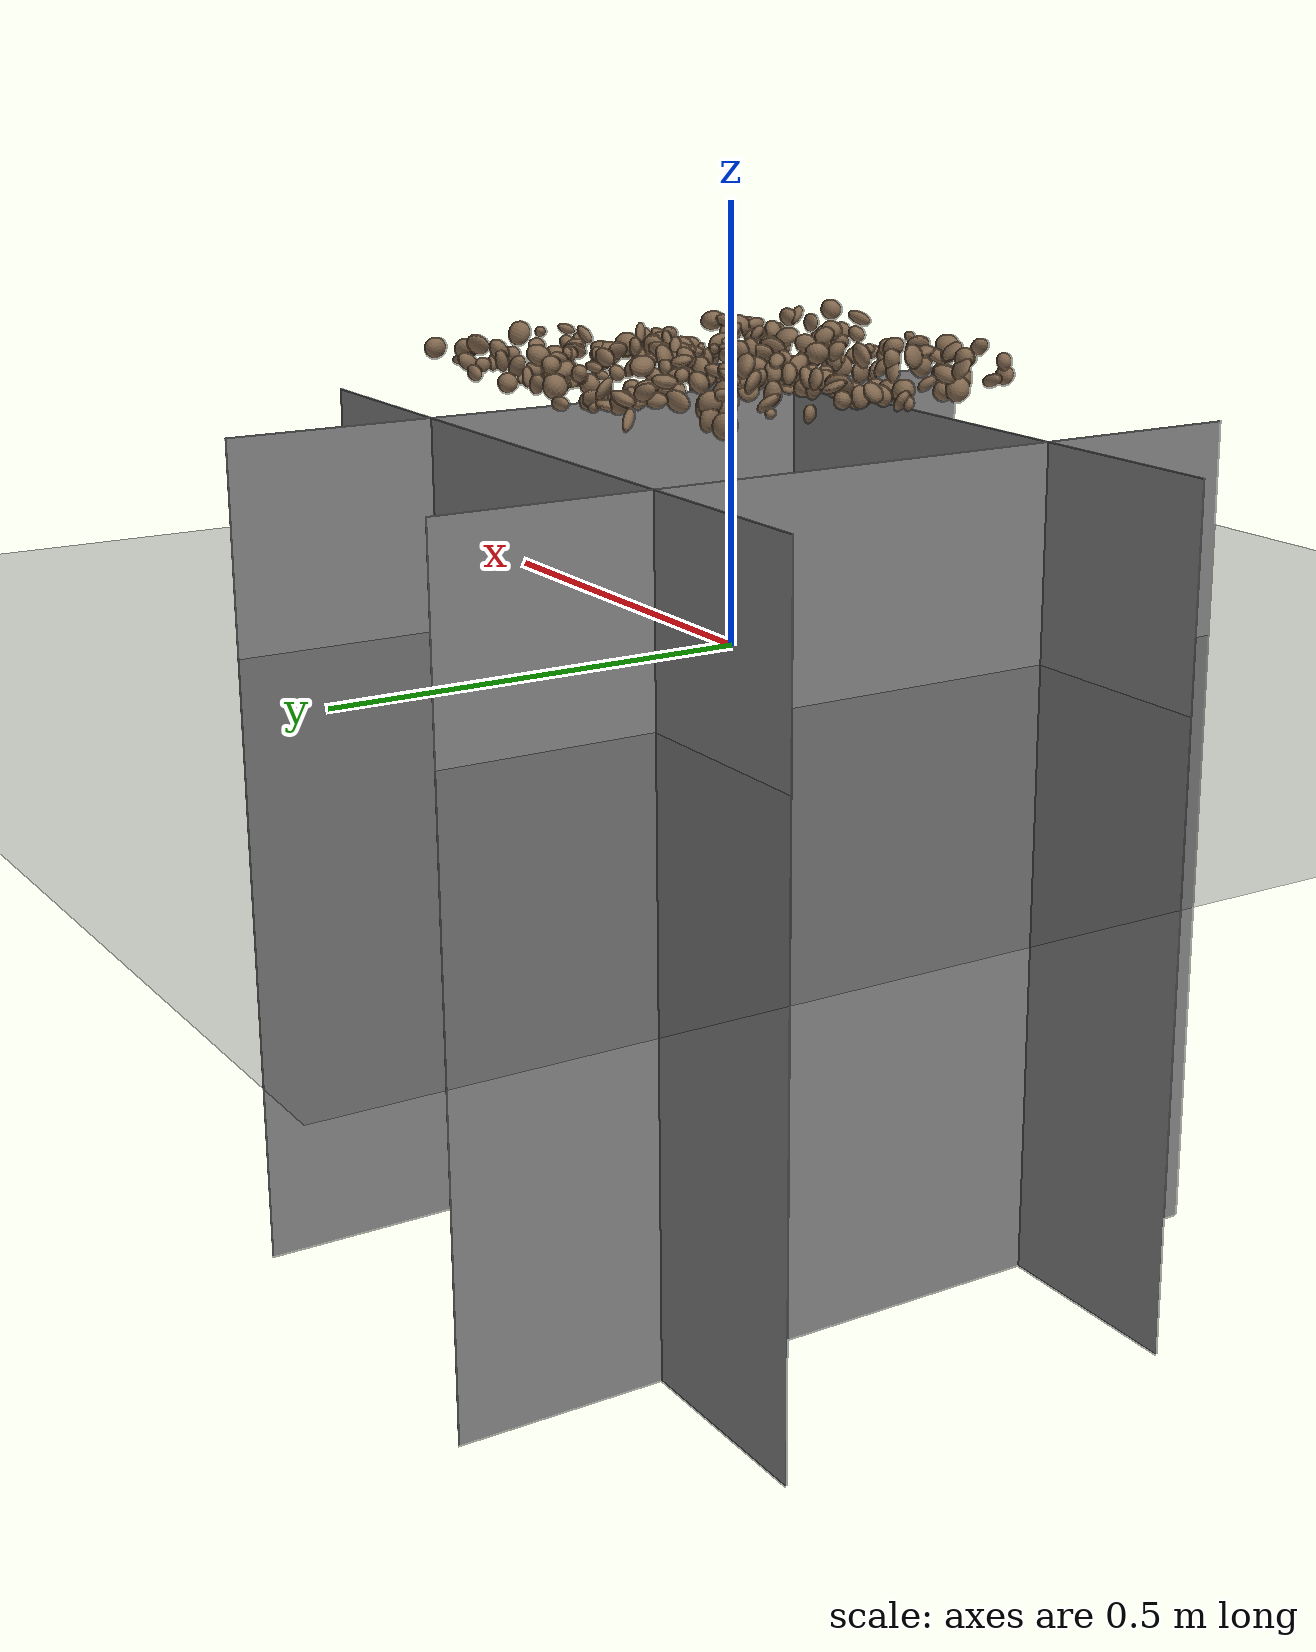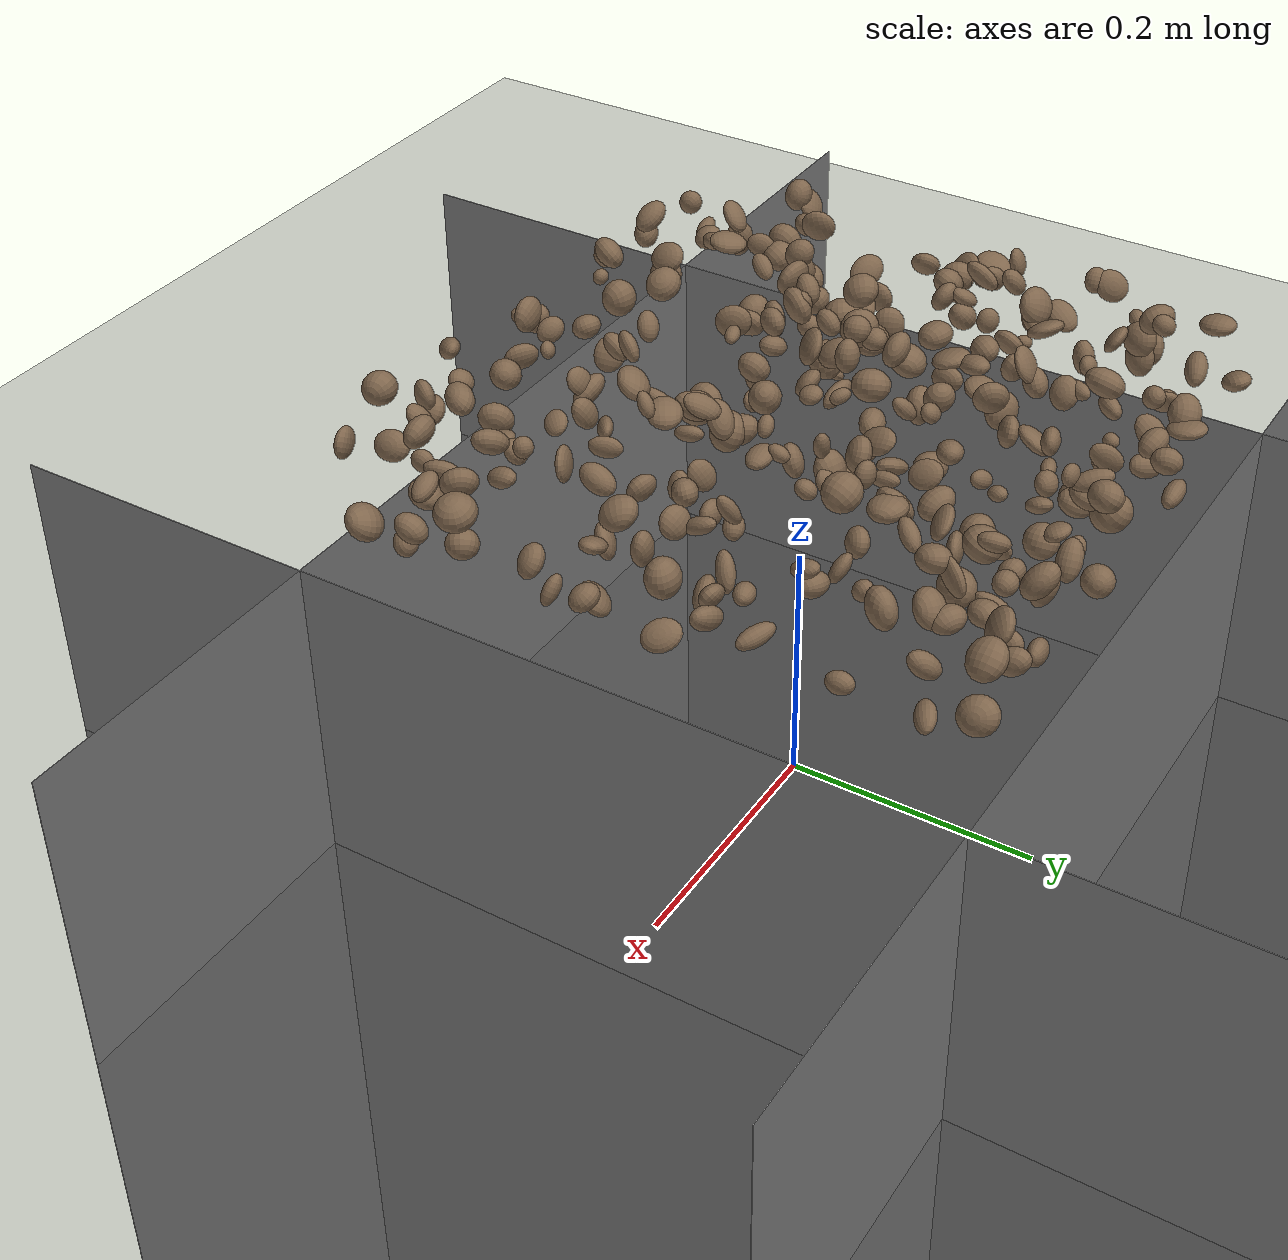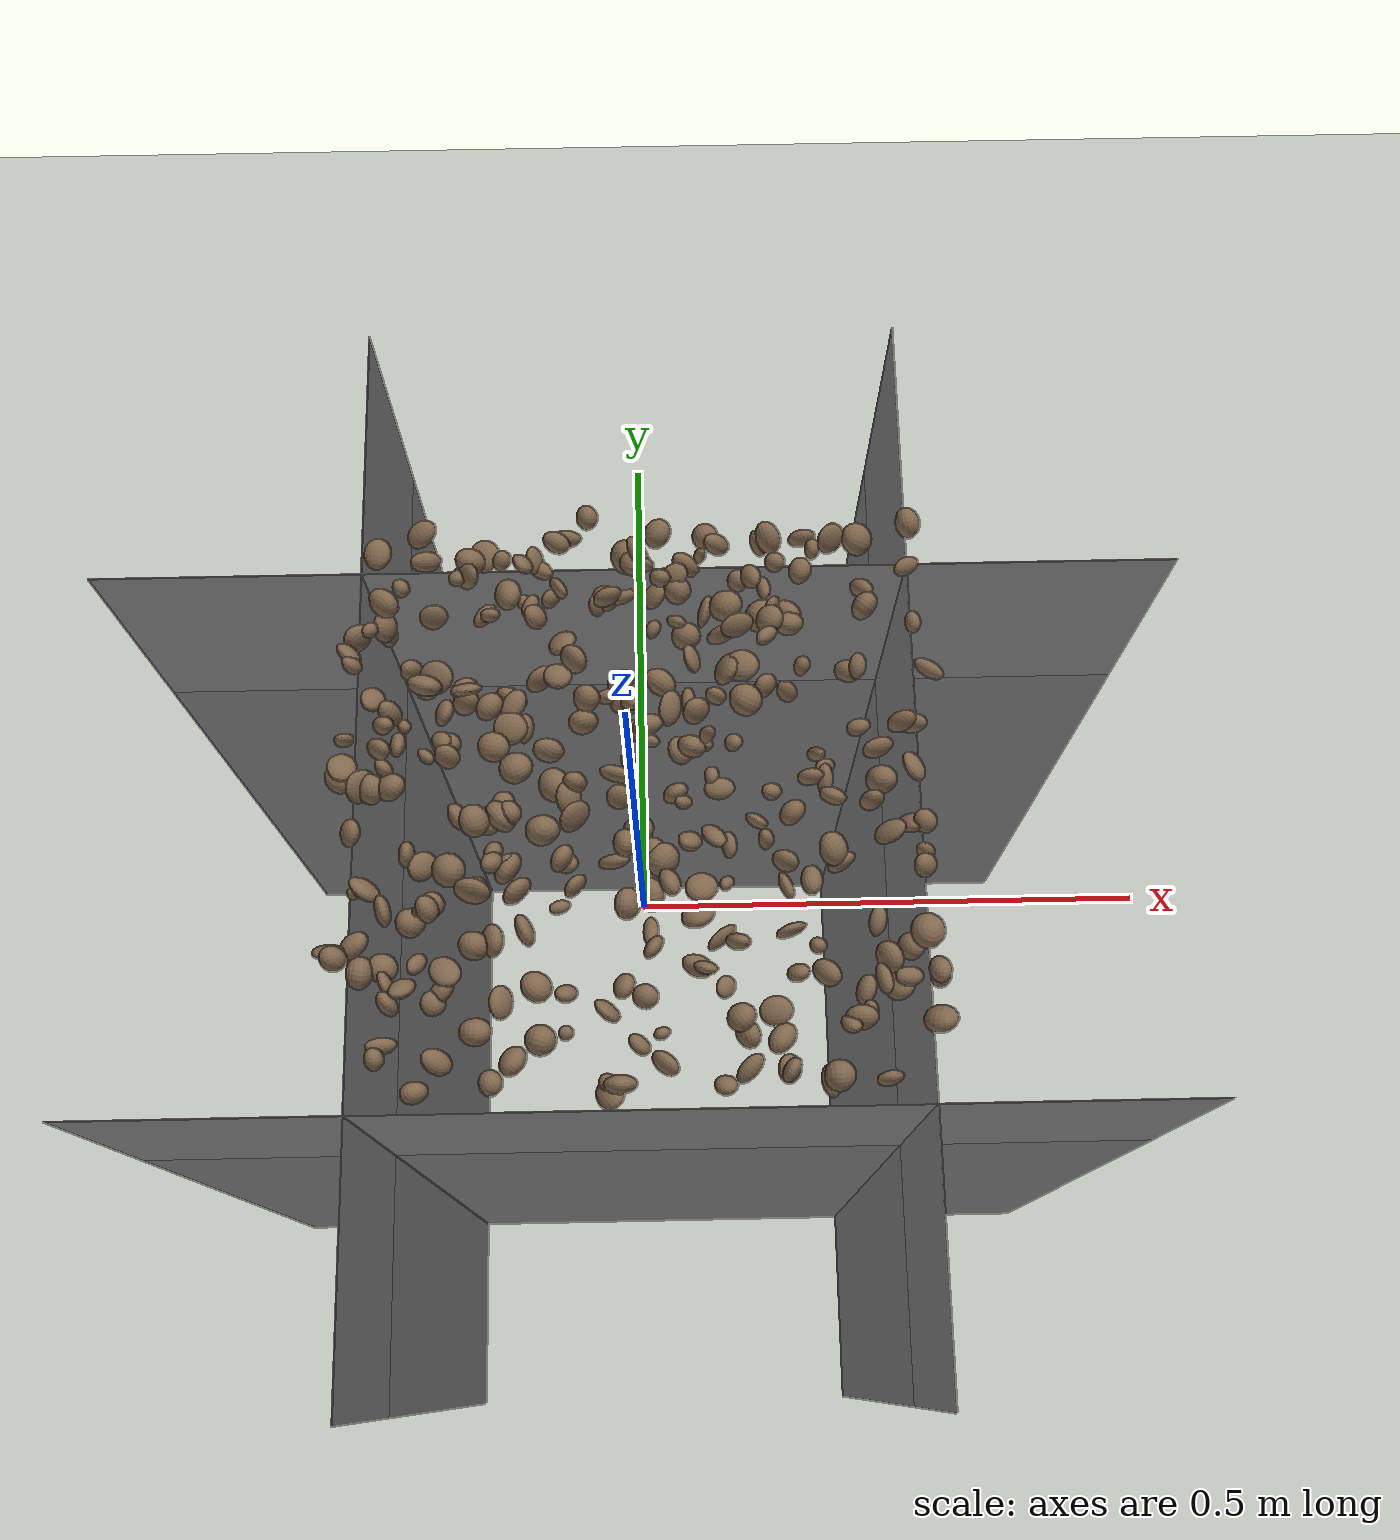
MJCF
<mujoco model="rocky_terrain_scene">

  <default>
    <default class="wall">
      <geom type="plane" size=".5 .5 .05" />
    </default>
  </default>

    <compiler angle="radian" inertiafromgeom="true" />
    <option timestep="0.002" gravity="0 0 -9.81" />

    <worldbody>

        <geom name="+x" class="wall" zaxis="1 0 0" pos="-.25 0 -.25" />
        <geom name="-x" class="wall" zaxis="-1 0 0" pos=".25 0 -.25" />
        <geom name="+y" class="wall" zaxis="0 1 0" pos="0 -.25 -.25" />
        <geom name="-y" class="wall" zaxis="0 -1 0" pos="0 .25 -.25" />

        <light name="sunlight" pos="5 5 5" dir="-1 -1 -1" diffuse="1 1 1" specular="0.5 0.5 0.5" ambient="0.5 0.5 0.5" />

        <geom name="ground_plane" type="plane" size="50 50 0.1" rgba="0.3 0.3 0.3 1" />

        <body name="rocky_terrain_body">

        </body>
    <body name="rock1" pos="-0.196892994164381 0.07700250606429743 0.30233634962338657"><joint type="free" /><geom type="ellipsoid" size="0.005591298021893736 0.005366043330090026 0.0063638438565754695" quat="0.4161710626519725 0.3536071338870138 0.09814646711305203 0.13207533634796162" rgba="0.5 0.4 0.3 1" /><inertial pos="-0.196892994164381 0.07700250606429743 0.30233634962338657" quat="0.4161710626519725 0.3536071338870138 0.09814646711305203 0.13207533634796162" mass="8.286974833000153e-05" /></body><body name="rock2" pos="0.14717349654711148 0.01321577756193898 0.33071023699028906"><joint type="free" /><geom type="ellipsoid" size="0.006638981843008615 0.009850984093945817 0.011234143647859504" quat="0.284425201518366 0.20056809122743088 0.20398727507251788 0.3110194321816852" rgba="0.5 0.4 0.3 1" /><inertial pos="0.14717349654711148 0.01321577756193898 0.33071023699028906" quat="0.284425201518366 0.20056809122743088 0.20398727507251788 0.3110194321816852" mass="6.238209142105477e-05" /></body><body name="rock3" pos="-0.04196095612706907 0.06707581735615759 0.3277599262728383"><joint type="free" /><geom type="ellipsoid" size="0.009824057976514528 0.014020005531705633 0.0122590624503227" quat="0.24600043846804032 0.2244971645770321 0.2312412378072077 0.29826115914771995" rgba="0.5 0.4 0.3 1" /><inertial pos="-0.04196095612706907 0.06707581735615759 0.3277599262728383" quat="0.24600043846804032 0.2244971645770321 0.2312412378072077 0.29826115914771995" mass="4.9061021535289675e-05" /></body><body name="rock4" pos="-0.09700835561850946 -0.07956187024961903 0.32494478179069153"><joint type="free" /><geom type="ellipsoid" size="0.007616285376229222 0.014074301808535833 0.013462011229577096" quat="0.2094622165848673 0.0819389233034346 0.21025616491290908 0.49834269519878904" rgba="0.5 0.4 0.3 1" /><inertial pos="-0.09700835561850946 -0.07956187024961903 0.32494478179069153" quat="0.2094622165848673 0.0819389233034346 0.21025616491290908 0.49834269519878904" mass="7.02865911538186e-05" /></body><body name="rock5" pos="-0.09119076824604277 0.06438377597551614 0.3223871079727267"><joint type="free" /><geom type="ellipsoid" size="0.012511860148933634 0.009713802021172863 0.006798510283089668" quat="0.2522382610144733 0.2765915994853259 0.1951583102647122 0.27601182923548856" rgba="0.5 0.4 0.3 1" /><inertial pos="-0.09119076824604277 0.06438377597551614 0.3223871079727267" quat="0.2522382610144733 0.2765915994853259 0.1951583102647122 0.27601182923548856" mass="1.6029694524354357e-05" /></body><body name="rock6" pos="-0.1198197754094017 0.07884524794455272 0.3366705666448422"><joint type="free" /><geom type="ellipsoid" size="0.012579328434179058 0.009277535442152825 0.00997840931922696" quat="0.24446101182829488 0.44898869608413394 0.1623477480817995 0.14420254400577168" rgba="0.5 0.4 0.3 1" /><inertial pos="-0.1198197754094017 0.07884524794455272 0.3366705666448422" quat="0.24446101182829488 0.44898869608413394 0.1623477480817995 0.14420254400577168" mass="3.956451178172831e-05" /></body><body name="rock7" pos="0.02612787455071819 0.22748637948958111 0.34894577380895714"><joint type="free" /><geom type="ellipsoid" size="0.007235626450170936 0.005189341328349846 0.005264902093259694" quat="0.3790637238372665 0.0580796780736899 0.055828086465399676 0.5070285116236438" rgba="0.5 0.4 0.3 1" /><inertial pos="0.02612787455071819 0.22748637948958111 0.34894577380895714" quat="0.3790637238372665 0.0580796780736899 0.055828086465399676 0.5070285116236438" mass="9.923633614201016e-05" /></body><body name="rock8" pos="-0.062283376970438564 0.10279804966022082 0.3420430791390779"><joint type="free" /><geom type="ellipsoid" size="0.011878323000547931 0.006126301582086812 0.011869624237290988" quat="0.17884546967108048 0.17227169204349183 0.3675175376248016 0.2813653006606261" rgba="0.5 0.4 0.3 1" /><inertial pos="-0.062283376970438564 0.10279804966022082 0.3420430791390779" quat="0.17884546967108048 0.17227169204349183 0.3675175376248016 0.2813653006606261" mass="8.801880807434851e-05" /></body><body name="rock9" pos="0.014871445125630878 -0.13381758892968365 0.34183935306216373"><joint type="free" /><geom type="ellipsoid" size="0.006077855256438185 0.00940398934496647 0.01230835075281855" quat="0.026565035026620262 0.19772397988979581 0.5152841343226935 0.2604268507608904" rgba="0.5 0.4 0.3 1" /><inertial pos="0.014871445125630878 -0.13381758892968365 0.34183935306216373" quat="0.026565035026620262 0.19772397988979581 0.5152841343226935 0.2604268507608904" mass="5.73992787087888e-05" /></body><body name="rock10" pos="-0.024215747662129805 -0.2380769638594032 0.31708060763311297"><joint type="free" /><geom type="ellipsoid" size="0.0071578543031611055 0.00841835686234066 0.006991673049502565" quat="0.1901662308043872 0.21605867690337566 0.2058537175298987 0.3879213747623384" rgba="0.5 0.4 0.3 1" /><inertial pos="-0.024215747662129805 -0.2380769638594032 0.31708060763311297" quat="0.1901662308043872 0.21605867690337566 0.2058537175298987 0.3879213747623384" mass="9.955583769404262e-05" /></body><body name="rock11" pos="-0.22257674969123398 0.15285681260562217 0.3322703022971976"><joint type="free" /><geom type="ellipsoid" size="0.007963455839588246 0.0056448534290461415 0.006031589032248145" quat="0.26910803489132773 0.4533544812176123 0.25758592603015046 0.019951557860909505" rgba="0.5 0.4 0.3 1" /><inertial pos="-0.22257674969123398 0.15285681260562217 0.3322703022971976" quat="0.26910803489132773 0.4533544812176123 0.25758592603015046 0.019951557860909505" mass="9.258911779063042e-05" /></body><body name="rock12" pos="0.219712944356188 -0.15969177577413368 0.33307802914429735"><joint type="free" /><geom type="ellipsoid" size="0.007990725922069033 0.012557149441334004 0.006329536508341116" quat="0.40255991621256737 0.103461612874634 0.06487635885357115 0.4291021120592275" rgba="0.5 0.4 0.3 1" /><inertial pos="0.219712944356188 -0.15969177577413368 0.33307802914429735" quat="0.40255991621256737 0.103461612874634 0.06487635885357115 0.4291021120592275" mass="3.0210224596020632e-05" /></body><body name="rock13" pos="-0.21396292580381449 0.03964725045175882 0.30108870033537755"><joint type="free" /><geom type="ellipsoid" size="0.008687207883319769 0.009904434113295155 0.00636676373224786" quat="0.18734351929742818 0.12682496071051552 0.32391690564332004 0.36191461434873634" rgba="0.5 0.4 0.3 1" /><inertial pos="-0.21396292580381449 0.03964725045175882 0.30108870033537755" quat="0.18734351929742818 0.12682496071051552 0.32391690564332004 0.36191461434873634" mass="3.4715233816905435e-05" /></body><body name="rock14" pos="-0.21479817096625997 0.21489739955381398 0.3495783615834529"><joint type="free" /><geom type="ellipsoid" size="0.01162039545626459 0.007060684124584736 0.013477399161008274" quat="0.026198895970480456 0.025936294223996806 0.44019971538268593 0.5076650944228368" rgba="0.5 0.4 0.3 1" /><inertial pos="-0.21479817096625997 0.21489739955381398 0.3495783615834529" quat="0.026198895970480456 0.025936294223996806 0.44019971538268593 0.5076650944228368" mass="4.352186851421255e-05" /></body><body name="rock15" pos="-0.13137314325561533 -0.08354775023011785 0.3420262708561189"><joint type="free" /><geom type="ellipsoid" size="0.008010154303344116 0.01427048636738722 0.014924205235129974" quat="0.31314021193297853 0.2256803644450529 0.2650321607875525 0.19614726283441608" rgba="0.5 0.4 0.3 1" /><inertial pos="-0.13137314325561533 -0.08354775023011785 0.3420262708561189" quat="0.31314021193297853 0.2256803644450529 0.2650321607875525 0.19614726283441608" mass="1.497385087161829e-05" /></body><body name="rock16" pos="-0.06166307624501516 -0.09413550285895722 0.32509611017517875"><joint type="free" /><geom type="ellipsoid" size="0.005707052915830231 0.005058873559963455 0.009160497272833499" quat="0.16966466613229922 0.2440529959188295 0.3046341475035521 0.28164819044531914" rgba="0.5 0.4 0.3 1" /><inertial pos="-0.06166307624501516 -0.09413550285895722 0.32509611017517875" quat="0.16966466613229922 0.2440529959188295 0.3046341475035521 0.28164819044531914" mass="5.9023652819271026e-05" /></body><body name="rock17" pos="-0.08033139429124247 0.21975790491412878 0.30857360141844054"><joint type="free" /><geom type="ellipsoid" size="0.0073620093203100746 0.008971396807926836 0.012738845966287087" quat="0.323596679119928 0.3387208966421325 0.05627002225692884 0.28141240198101064" rgba="0.5 0.4 0.3 1" /><inertial pos="-0.08033139429124247 0.21975790491412878 0.30857360141844054" quat="0.323596679119928 0.3387208966421325 0.05627002225692884 0.28141240198101064" mass="9.764045824061568e-05" /></body><body name="rock18" pos="0.10174491664089674 0.189508088021756 0.34575007202535873"><joint type="free" /><geom type="ellipsoid" size="0.01111081852548612 0.00879522923373315 0.006520967568008131" quat="0.1562412488217111 0.25966983529781523 0.4599830898855479 0.12410582599492581" rgba="0.5 0.4 0.3 1" /><inertial pos="0.10174491664089674 0.189508088021756 0.34575007202535873" quat="0.1562412488217111 0.25966983529781523 0.4599830898855479 0.12410582599492581" mass="9.518121747720039e-05" /></body><body name="rock19" pos="0.24033939757883843 0.24576754433675407 0.33065551181289676"><joint type="free" /><geom type="ellipsoid" size="0.013343922529101132 0.012655018177089956 0.010324786231280133" quat="0.21669998947486172 0.23308460440686257 0.161040127872077 0.38917527824619874" rgba="0.5 0.4 0.3 1" /><inertial pos="0.24033939757883843 0.24576754433675407 0.33065551181289676" quat="0.21669998947486172 0.23308460440686257 0.161040127872077 0.38917527824619874" mass="6.981007646989035e-05" /></body><body name="rock20" pos="0.09241573966404026 0.1114133594036481 0.3375482437574212"><joint type="free" /><geom type="ellipsoid" size="0.00826811258526287 0.013564182754573599 0.014532163285236956" quat="0.48489232121530185 0.01589548926074199 0.46341873455536303 0.035793454968593076" rgba="0.5 0.4 0.3 1" /><inertial pos="0.09241573966404026 0.1114133594036481 0.3375482437574212" quat="0.48489232121530185 0.01589548926074199 0.46341873455536303 0.035793454968593076" mass="2.3723383389323394e-05" /></body><body name="rock21" pos="0.18239499204728954 0.10694290210245105 0.33270199303530895"><joint type="free" /><geom type="ellipsoid" size="0.00930465540713257 0.008492916865872115 0.012043373795856582" quat="0.2321263923238516 0.3101067663895463 0.12312314870296381 0.3346436925836383" rgba="0.5 0.4 0.3 1" /><inertial pos="0.18239499204728954 0.10694290210245105 0.33270199303530895" quat="0.2321263923238516 0.3101067663895463 0.12312314870296381 0.3346436925836383" mass="1.2113210763608891e-05" /></body><body name="rock22" pos="0.046102781677233806 0.15425618415797626 0.3065977024697241"><joint type="free" /><geom type="ellipsoid" size="0.012473316480473982 0.011507531472764374 0.01252166403705503" quat="0.10075195286869845 0.5785333648903993 0.022309055363788504 0.29840562687711375" rgba="0.5 0.4 0.3 1" /><inertial pos="0.046102781677233806 0.15425618415797626 0.3065977024697241" quat="0.10075195286869845 0.5785333648903993 0.022309055363788504 0.29840562687711375" mass="4.1300727531896565e-05" /></body><body name="rock23" pos="-0.14001839831182133 0.22301574914626987 0.3189260774899282"><joint type="free" /><geom type="ellipsoid" size="0.010796951227094821 0.014536640059695061 0.012128016715168888" quat="0.3483592640337127 0.3236776179593157 0.00991334547837296 0.3180497725285986" rgba="0.5 0.4 0.3 1" /><inertial pos="-0.14001839831182133 0.22301574914626987 0.3189260774899282" quat="0.3483592640337127 0.3236776179593157 0.00991334547837296 0.3180497725285986" mass="3.133102822554018e-05" /></body><body name="rock24" pos="0.01807441628263068 0.15469227643631756 0.3203209941852481"><joint type="free" /><geom type="ellipsoid" size="0.00810814804039648 0.005472244207658682 0.005828143350592215" quat="0.2270303403568596 0.38048040059145877 0.16825209659252235 0.22423716245915928" rgba="0.5 0.4 0.3 1" /><inertial pos="0.01807441628263068 0.15469227643631756 0.3203209941852481" quat="0.2270303403568596 0.38048040059145877 0.16825209659252235 0.22423716245915928" mass="8.526025876209653e-05" /></body><body name="rock25" pos="0.16506827479039488 -0.002957425062562802 0.3285114338156311"><joint type="free" /><geom type="ellipsoid" size="0.006882201565980517 0.011784661346972255 0.011653163755438588" quat="0.17031257493702823 0.39936186291150694 0.21311582076330568 0.21720974138815904" rgba="0.5 0.4 0.3 1" /><inertial pos="0.16506827479039488 -0.002957425062562802 0.3285114338156311" quat="0.17031257493702823 0.39936186291150694 0.21311582076330568 0.21720974138815904" mass="9.087265208174649e-05" /></body><body name="rock26" pos="0.03940718962886419 0.04802370855510779 0.30776705674708005"><joint type="free" /><geom type="ellipsoid" size="0.012028936194827084 0.01221690022126648 0.00820275319645614" quat="0.02766005351521301 0.25916788853890055 0.026996355552296604 0.6861757023935899" rgba="0.5 0.4 0.3 1" /><inertial pos="0.03940718962886419 0.04802370855510779 0.30776705674708005" quat="0.02766005351521301 0.25916788853890055 0.026996355552296604 0.6861757023935899" mass="6.453117268703912e-05" /></body><body name="rock27" pos="-0.06378587644385414 0.19724545819252348 0.31658095571134437"><joint type="free" /><geom type="ellipsoid" size="0.013936185040729483 0.009250358149814408 0.005243692593009601" quat="0.2973089532634072 0.06385401603487824 0.38628626730669957 0.2525507633950149" rgba="0.5 0.4 0.3 1" /><inertial pos="-0.06378587644385414 0.19724545819252348 0.31658095571134437" quat="0.2973089532634072 0.06385401603487824 0.38628626730669957 0.2525507633950149" mass="1.2989214349678705e-05" /></body><body name="rock28" pos="0.15876259057494924 -0.24211088555389942 0.3491274225610364"><joint type="free" /><geom type="ellipsoid" size="0.012982811114740436 0.012063845640172505 0.012418425949036669" quat="0.13606419162067845 0.35236095650481736 0.17127921514441516 0.340295636730089" rgba="0.5 0.4 0.3 1" /><inertial pos="0.15876259057494924 -0.24211088555389942 0.3491274225610364" quat="0.13606419162067845 0.35236095650481736 0.17127921514441516 0.340295636730089" mass="4.965658504304565e-05" /></body><body name="rock29" pos="0.09469350039454716 0.07951538961178456 0.3397413762570896"><joint type="free" /><geom type="ellipsoid" size="0.012793833864824473 0.013801068634920512 0.014126302927450176" quat="0.09950646742506608 0.553168400496773 0.037201278599661436 0.3101238534784994" rgba="0.5 0.4 0.3 1" /><inertial pos="0.09469350039454716 0.07951538961178456 0.3397413762570896" quat="0.09950646742506608 0.553168400496773 0.037201278599661436 0.3101238534784994" mass="3.363332261345972e-05" /></body><body name="rock30" pos="-0.10681817567808755 -0.17755500035322241 0.3439436313174563"><joint type="free" /><geom type="ellipsoid" size="0.013876186395081046 0.011876252971203103 0.006452803059312102" quat="0.3223422753416246 0.20170209484686513 0.1130179148415433 0.3629377149699671" rgba="0.5 0.4 0.3 1" /><inertial pos="-0.10681817567808755 -0.17755500035322241 0.3439436313174563" quat="0.3223422753416246 0.20170209484686513 0.1130179148415433 0.3629377149699671" mass="5.205337966286188e-05" /></body><body name="rock31" pos="-0.22622196636629555 -0.1429838668576463 0.3129421035386913"><joint type="free" /><geom type="ellipsoid" size="0.013787666646472737 0.01431175339979264 0.011300628302738435" quat="0.19387878722284377 0.3418370997761331 0.1990385535682092 0.26524555943281397" rgba="0.5 0.4 0.3 1" /><inertial pos="-0.22622196636629555 -0.1429838668576463 0.3129421035386913" quat="0.19387878722284377 0.3418370997761331 0.1990385535682092 0.26524555943281397" mass="9.910843321449234e-05" /></body><body name="rock32" pos="-0.007353407602300965 -0.04483861141194828 0.3410570400580699"><joint type="free" /><geom type="ellipsoid" size="0.011110052742129409 0.01199897346940495 0.009576417519544623" quat="0.11421314246946966 0.44088052171174996 0.14428539465811357 0.3006209411606668" rgba="0.5 0.4 0.3 1" /><inertial pos="-0.007353407602300965 -0.04483861141194828 0.3410570400580699" quat="0.11421314246946966 0.44088052171174996 0.14428539465811357 0.3006209411606668" mass="2.8725383395105154e-05" /></body><body name="rock33" pos="0.2249907419192776 0.06015112181056931 0.33349288248288483"><joint type="free" /><geom type="ellipsoid" size="0.00632613372220269 0.013277629925888827 0.009038172637161626" quat="0.24687356277654857 0.35019863015755964 0.369814118598883 0.03311368846700883" rgba="0.5 0.4 0.3 1" /><inertial pos="0.2249907419192776 0.06015112181056931 0.33349288248288483" quat="0.24687356277654857 0.35019863015755964 0.369814118598883 0.03311368846700883" mass="5.8357160521764484e-05" /></body><body name="rock34" pos="0.08918926474177546 -0.2349481943895972 0.34717274239328416"><joint type="free" /><geom type="ellipsoid" size="0.006713178819217611 0.008293552779922747 0.014502534412815071" quat="0.31241228326646314 0.009747293893988354 0.3132424563040409 0.36459796653550763" rgba="0.5 0.4 0.3 1" /><inertial pos="0.08918926474177546 -0.2349481943895972 0.34717274239328416" quat="0.31241228326646314 0.009747293893988354 0.3132424563040409 0.36459796653550763" mass="3.0272802568281375e-05" /></body><body name="rock35" pos="-0.0532785723616121 -0.005301349935159183 0.34135274308244473"><joint type="free" /><geom type="ellipsoid" size="0.013912789667319927 0.011410756429178288 0.007180849107934768" quat="0.320587261528213 0.21579468148219375 0.03128755096164803 0.4323305060279452" rgba="0.5 0.4 0.3 1" /><inertial pos="-0.0532785723616121 -0.005301349935159183 0.34135274308244473" quat="0.320587261528213 0.21579468148219375 0.03128755096164803 0.4323305060279452" mass="8.152021651815116e-05" /></body><body name="rock36" pos="0.08406980961914912 0.04762352779139922 0.3244144829574031"><joint type="free" /><geom type="ellipsoid" size="0.007620089778529982 0.00672401562519281 0.008285297214553825" quat="0.4787012037978411 0.24742204625830982 0.04944682986462203 0.22442992007922713" rgba="0.5 0.4 0.3 1" /><inertial pos="0.08406980961914912 0.04762352779139922 0.3244144829574031" quat="0.4787012037978411 0.24742204625830982 0.04944682986462203 0.22442992007922713" mass="5.374050779847866e-05" /></body><body name="rock37" pos="0.003579189055947285 0.21117714069110638 0.3326207535176733"><joint type="free" /><geom type="ellipsoid" size="0.01309592950784309 0.009479099346934732 0.013753864012984517" quat="0.4352167825222978 0.24900766341766095 0.19277781384056 0.12299774021948125" rgba="0.5 0.4 0.3 1" /><inertial pos="0.003579189055947285 0.21117714069110638 0.3326207535176733" quat="0.4352167825222978 0.24900766341766095 0.19277781384056 0.12299774021948125" mass="1.4595140693962887e-05" /></body><body name="rock38" pos="0.07111541740191085 0.005338283143153988 0.32838454015502405"><joint type="free" /><geom type="ellipsoid" size="0.009399480076272046 0.005945846003805164 0.012887335498069231" quat="0.21131339577994077 0.2645049202040827 0.26519121674904766 0.25899046726692887" rgba="0.5 0.4 0.3 1" /><inertial pos="0.07111541740191085 0.005338283143153988 0.32838454015502405" quat="0.21131339577994077 0.2645049202040827 0.26519121674904766 0.25899046726692887" mass="2.8715786905274474e-05" /></body><body name="rock39" pos="0.010421906492098842 0.05598058178978438 0.315074933233843"><joint type="free" /><geom type="ellipsoid" size="0.005670232234048378 0.006115072797738692 0.012090411305955829" quat="0.25973896184595346 0.3176127931861247 0.2175107549313956 0.2051374900365263" rgba="0.5 0.4 0.3 1" /><inertial pos="0.010421906492098842 0.05598058178978438 0.315074933233843" quat="0.25973896184595346 0.3176127931861247 0.2175107549313956 0.2051374900365263" mass="7.049094303937009e-05" /></body><body name="rock40" pos="0.0710149278347666 -0.24106236965289196 0.3085504397020109"><joint type="free" /><geom type="ellipsoid" size="0.007189449042943679 0.009834372416446111 0.009595884435645925" quat="0.03536034709400173 0.41440786157980636 0.23871135402053087 0.31152043730566104" rgba="0.5 0.4 0.3 1" /><inertial pos="0.0710149278347666 -0.24106236965289196 0.3085504397020109" quat="0.03536034709400173 0.41440786157980636 0.23871135402053087 0.31152043730566104" mass="6.311420177828713e-05" /></body><body name="rock41" pos="0.022677179429163585 -0.047954760173677224 0.3038883583038172"><joint type="free" /><geom type="ellipsoid" size="0.014987926711822044 0.014968261481414166 0.012539704785634992" quat="0.36301737528195827 0.2982978660372893 0.05686059516940309 0.2818241635113493" rgba="0.5 0.4 0.3 1" /><inertial pos="0.022677179429163585 -0.047954760173677224 0.3038883583038172" quat="0.36301737528195827 0.2982978660372893 0.05686059516940309 0.2818241635113493" mass="2.218507795946107e-05" /></body><body name="rock42" pos="-0.03832080794992471 0.08294131716317094 0.3408895831704921"><joint type="free" /><geom type="ellipsoid" size="0.011222694059140935 0.009946166672657526 0.012267915852468343" quat="0.17908328512662103 0.07550703837089615 0.13356831436799116 0.6118413621344917" rgba="0.5 0.4 0.3 1" /><inertial pos="-0.03832080794992471 0.08294131716317094 0.3408895831704921" quat="0.17908328512662103 0.07550703837089615 0.13356831436799116 0.6118413621344917" mass="8.433453908987907e-05" /></body><body name="rock43" pos="0.23835033048630527 0.0323489269586576 0.3006191165576019"><joint type="free" /><geom type="ellipsoid" size="0.0137940426601026 0.010980412398215355 0.005931268085869867" quat="0.2144251381525779 0.17045790904152947 0.13336847227658355 0.4817484805293091" rgba="0.5 0.4 0.3 1" /><inertial pos="0.23835033048630527 0.0323489269586576 0.3006191165576019" quat="0.2144251381525779 0.17045790904152947 0.13336847227658355 0.4817484805293091" mass="6.889895891428153e-05" /></body><body name="rock44" pos="-0.06053798469393784 0.1461025322921693 0.31505413973087126"><joint type="free" /><geom type="ellipsoid" size="0.014257347510018573 0.006207771747258606 0.012287098336372045" quat="0.3742399075848637 0.1315693974876518 0.26048214064663405 0.2337085542808505" rgba="0.5 0.4 0.3 1" /><inertial pos="-0.06053798469393784 0.1461025322921693 0.31505413973087126" quat="0.3742399075848637 0.1315693974876518 0.26048214064663405 0.2337085542808505" mass="3.608882376307551e-05" /></body><body name="rock45" pos="-0.13095734650553348 -0.19418808295229595 0.31335652446824114"><joint type="free" /><geom type="ellipsoid" size="0.011471084865470882 0.012806536986035474 0.013574039421234151" quat="0.23243881150490123 0.2744740668606034 0.17221673907507587 0.32087038255941946" rgba="0.5 0.4 0.3 1" /><inertial pos="-0.13095734650553348 -0.19418808295229595 0.31335652446824114" quat="0.23243881150490123 0.2744740668606034 0.17221673907507587 0.32087038255941946" mass="9.892833492016533e-05" /></body><body name="rock46" pos="0.23936837969220381 0.21278815414441182 0.31501666542529766"><joint type="free" /><geom type="ellipsoid" size="0.007615230066017613 0.005804437190380378 0.012419808069870896" quat="0.056036003857065905 0.33263747168574065 0.26979203991935463 0.34153448453783886" rgba="0.5 0.4 0.3 1" /><inertial pos="0.23936837969220381 0.21278815414441182 0.31501666542529766" quat="0.056036003857065905 0.33263747168574065 0.26979203991935463 0.34153448453783886" mass="7.060998916470319e-05" /></body><body name="rock47" pos="0.1247001497968599 -0.05406677124475817 0.31353252049868824"><joint type="free" /><geom type="ellipsoid" size="0.007149547661902568 0.011096021013400185 0.01130927932977088" quat="0.27850666240754723 0.3287627866448456 0.29057052268159883 0.10216002826600833" rgba="0.5 0.4 0.3 1" /><inertial pos="0.1247001497968599 -0.05406677124475817 0.31353252049868824" quat="0.27850666240754723 0.3287627866448456 0.29057052268159883 0.10216002826600833" mass="4.6391670761934505e-05" /></body><body name="rock48" pos="-0.23745996234146166 0.12507531747335382 0.34441990247115006"><joint type="free" /><geom type="ellipsoid" size="0.013651556610355609 0.011406091672756264 0.006248075950842926" quat="0.32182849987082196 0.021421230964728075 0.3098166179646878 0.3469336511997621" rgba="0.5 0.4 0.3 1" /><inertial pos="-0.23745996234146166 0.12507531747335382 0.34441990247115006" quat="0.32182849987082196 0.021421230964728075 0.3098166179646878 0.3469336511997621" mass="2.3197592627291897e-05" /></body><body name="rock49" pos="-0.2212057630657117 0.09534401406904525 0.31841743411711426"><joint type="free" /><geom type="ellipsoid" size="0.01402307379595824 0.005903358718959278 0.010368897459758985" quat="0.3064661249232185 0.2976114872410466 0.32898601278795603 0.06693637504777886" rgba="0.5 0.4 0.3 1" /><inertial pos="-0.2212057630657117 0.09534401406904525 0.31841743411711426" quat="0.3064661249232185 0.2976114872410466 0.32898601278795603 0.06693637504777886" mass="8.845938864774891e-05" /></body><body name="rock50" pos="-0.09393548306893512 0.21568290792565797 0.32646598956168016"><joint type="free" /><geom type="ellipsoid" size="0.014013068891877836 0.005900866412395564 0.009833408866859017" quat="0.30733858584983026 0.2716347063775554 0.40905498159215326 0.011971726180461119" rgba="0.5 0.4 0.3 1" /><inertial pos="-0.09393548306893512 0.21568290792565797 0.32646598956168016" quat="0.30733858584983026 0.2716347063775554 0.40905498159215326 0.011971726180461119" mass="2.5260698832001766e-05" /></body><body name="rock51" pos="-0.23915766403790972 0.04918910330842119 0.34154681943828036"><joint type="free" /><geom type="ellipsoid" size="0.011621981714292311 0.005462547722937765 0.00849863901306995" quat="0.4273298293481594 0.030971925507804834 0.46150556506401935 0.08019268008001641" rgba="0.5 0.4 0.3 1" /><inertial pos="-0.23915766403790972 0.04918910330842119 0.34154681943828036" quat="0.4273298293481594 0.030971925507804834 0.46150556506401935 0.08019268008001641" mass="5.8596891426084335e-05" /></body><body name="rock52" pos="-0.15019652754040497 0.20750645253695826 0.3189354634085268"><joint type="free" /><geom type="ellipsoid" size="0.008292733117061166 0.006304900778426672 0.009012468582170603" quat="0.25164924356420554 0.10688708372458935 0.39664718332401055 0.24481648938719464" rgba="0.5 0.4 0.3 1" /><inertial pos="-0.15019652754040497 0.20750645253695826 0.3189354634085268" quat="0.25164924356420554 0.10688708372458935 0.39664718332401055 0.24481648938719464" mass="4.564530980902123e-05" /></body><body name="rock53" pos="0.20467886621804132 -0.1432274322393905 0.33292665782273073"><joint type="free" /><geom type="ellipsoid" size="0.013608183947895536 0.012073001143406308 0.00926984486480614" quat="0.05866075635262533 0.3145381461633748 0.3440768202517728 0.2827242772322271" rgba="0.5 0.4 0.3 1" /><inertial pos="0.20467886621804132 -0.1432274322393905 0.33292665782273073" quat="0.05866075635262533 0.3145381461633748 0.3440768202517728 0.2827242772322271" mass="6.874815259666866e-05" /></body><body name="rock54" pos="-0.014263054911436202 0.017272729335576442 0.3356201881673955"><joint type="free" /><geom type="ellipsoid" size="0.014208531390040639 0.006133213007569948 0.008020067457896204" quat="0.0577287720841904 0.10777881980995055 0.07014435397500939 0.7643480541308496" rgba="0.5 0.4 0.3 1" /><inertial pos="-0.014263054911436202 0.017272729335576442 0.3356201881673955" quat="0.0577287720841904 0.10777881980995055 0.07014435397500939 0.7643480541308496" mass="7.341888254919581e-05" /></body><body name="rock55" pos="0.15361937215122207 -0.155160590037063 0.3320556072085545"><joint type="free" /><geom type="ellipsoid" size="0.013475817026412894 0.010639066321422785 0.008473561588057357" quat="0.1830205454637261 0.13057091699820209 0.4963157700036653 0.19009276753440654" rgba="0.5 0.4 0.3 1" /><inertial pos="0.15361937215122207 -0.155160590037063 0.3320556072085545" quat="0.1830205454637261 0.13057091699820209 0.4963157700036653 0.19009276753440654" mass="1.910993266744595e-05" /></body><body name="rock56" pos="0.10926797050948961 -0.034718720347127696 0.3127538144138542"><joint type="free" /><geom type="ellipsoid" size="0.007584560906683441 0.011996517503350027 0.006508517306534858" quat="0.2958031930227358 0.23431319054620475 0.23370648148648923 0.23617713494457018" rgba="0.5 0.4 0.3 1" /><inertial pos="0.10926797050948961 -0.034718720347127696 0.3127538144138542" quat="0.2958031930227358 0.23431319054620475 0.23370648148648923 0.23617713494457018" mass="9.017344260495825e-05" /></body><body name="rock57" pos="-0.20820776094675036 -0.21903991201553052 0.33440509152736564"><joint type="free" /><geom type="ellipsoid" size="0.009781590494273198 0.008984012489034156 0.007984632837766155" quat="0.05036001107811083 0.41674466246841235 0.12790785931906337 0.4049874671344134" rgba="0.5 0.4 0.3 1" /><inertial pos="-0.20820776094675036 -0.21903991201553052 0.33440509152736564" quat="0.05036001107811083 0.41674466246841235 0.12790785931906337 0.4049874671344134" mass="2.420079159939591e-05" /></body><body name="rock58" pos="-0.13263331040275766 -0.06914606028077264 0.30439271749920715"><joint type="free" /><geom type="ellipsoid" size="0.00919582004085768 0.008572312045442768 0.009242723452628141" quat="0.3951451455723136 0.10415959262034626 0.06049217396366797 0.4402030878436722" rgba="0.5 0.4 0.3 1" /><inertial pos="-0.13263331040275766 -0.06914606028077264 0.30439271749920715" quat="0.3951451455723136 0.10415959262034626 0.06049217396366797 0.4402030878436722" mass="2.4564468930984423e-05" /></body><body name="rock59" pos="0.15772863700680312 0.22825492062080704 0.3200035250195487"><joint type="free" /><geom type="ellipsoid" size="0.008909927169400665 0.00907896055417172 0.006523395475421507" quat="0.1965216780188794 0.325811769456199 0.12004552791525581 0.3576210246096657" rgba="0.5 0.4 0.3 1" /><inertial pos="0.15772863700680312 0.22825492062080704 0.3200035250195487" quat="0.1965216780188794 0.325811769456199 0.12004552791525581 0.3576210246096657" mass="3.45310300747699e-05" /></body><body name="rock60" pos="-0.1561749422664046 -0.05417674547760898 0.30610458831992704"><joint type="free" /><geom type="ellipsoid" size="0.014338546355520322 0.014297672718515099 0.013216238364847147" quat="0.0002729034822444382 0.46953002102224 0.328277605087794 0.20191947040772143" rgba="0.5 0.4 0.3 1" /><inertial pos="-0.1561749422664046 -0.05417674547760898 0.30610458831992704" quat="0.0002729034822444382 0.46953002102224 0.328277605087794 0.20191947040772143" mass="1.4060957007861508e-05" /></body><body name="rock61" pos="0.14572246133359107 0.2051991619610793 0.3254080737266129"><joint type="free" /><geom type="ellipsoid" size="0.011503707144430055 0.009091724875197892 0.009600889858142149" quat="0.3000600473260167 0.27453447478175336 0.1755645278656876 0.2498409500265423" rgba="0.5 0.4 0.3 1" /><inertial pos="0.14572246133359107 0.2051991619610793 0.3254080737266129" quat="0.3000600473260167 0.27453447478175336 0.1755645278656876 0.2498409500265423" mass="2.3085035041112014e-05" /></body><body name="rock62" pos="0.12217562997868003 -0.22993810051235647 0.31505423563230267"><joint type="free" /><geom type="ellipsoid" size="0.011678608132217442 0.012606033091536593 0.0077250840748219005" quat="0.48442986688102685 0.14463706110225316 0.20586958099483618 0.1650634910218837" rgba="0.5 0.4 0.3 1" /><inertial pos="0.12217562997868003 -0.22993810051235647 0.31505423563230267" quat="0.48442986688102685 0.14463706110225316 0.20586958099483618 0.1650634910218837" mass="1.1205631721388911e-05" /></body><body name="rock63" pos="0.0465603904864903 0.08579939932075825 0.32411741411398837"><joint type="free" /><geom type="ellipsoid" size="0.011719216299259112 0.006213968713300591 0.0055964901223470535" quat="0.17490578502428641 0.32600684447878986 0.2780273268831764 0.22106004361374737" rgba="0.5 0.4 0.3 1" /><inertial pos="0.0465603904864903 0.08579939932075825 0.32411741411398837" quat="0.17490578502428641 0.32600684447878986 0.2780273268831764 0.22106004361374737" mass="3.313093990541229e-05" /></body><body name="rock64" pos="-0.09899796566095065 0.029326289399444982 0.3224308845611652"><joint type="free" /><geom type="ellipsoid" size="0.011589775761384272 0.014056476725463757 0.014166574227715525" quat="0.006019126817922141 0.3884807388308717 0.168199201857323 0.43730093249388324" rgba="0.5 0.4 0.3 1" /><inertial pos="-0.09899796566095065 0.029326289399444982 0.3224308845611652" quat="0.006019126817922141 0.3884807388308717 0.168199201857323 0.43730093249388324" mass="5.013614158022711e-05" /></body><body name="rock65" pos="0.0022037531788088316 -0.2100044721075603 0.32601807020479767"><joint type="free" /><geom type="ellipsoid" size="0.009066106480523379 0.01098424283785704 0.006515192111198653" quat="0.37881038097394215 0.006445427712582595 0.3129751663654573 0.30176902494801794" rgba="0.5 0.4 0.3 1" /><inertial pos="0.0022037531788088316 -0.2100044721075603 0.32601807020479767" quat="0.37881038097394215 0.006445427712582595 0.3129751663654573 0.30176902494801794" mass="4.22292901478182e-05" /></body><body name="rock66" pos="-0.2425379119701514 0.02859684080504893 0.3320602754740962"><joint type="free" /><geom type="ellipsoid" size="0.014062005510299694 0.005438998197787205 0.012196146418129643" quat="0.28091237418639503 0.26747639961684055 0.297938054611201 0.15367317158556346" rgba="0.5 0.4 0.3 1" /><inertial pos="-0.2425379119701514 0.02859684080504893 0.3320602754740962" quat="0.28091237418639503 0.26747639961684055 0.297938054611201 0.15367317158556346" mass="7.705268701598068e-05" /></body><body name="rock67" pos="-0.11926510001375906 -0.11454443088704208 0.3003163762332896"><joint type="free" /><geom type="ellipsoid" size="0.00829259403013634 0.014133299285285901 0.013012306140980236" quat="0.6815606244039109 0.11098406196259944 0.18589721453875388 0.02155809909473574" rgba="0.5 0.4 0.3 1" /><inertial pos="-0.11926510001375906 -0.11454443088704208 0.3003163762332896" quat="0.6815606244039109 0.11098406196259944 0.18589721453875388 0.02155809909473574" mass="3.4601583702381456e-05" /></body><body name="rock68" pos="-0.07072912767207079 0.191257327642485 0.3094003052772413"><joint type="free" /><geom type="ellipsoid" size="0.006262474506218482 0.008417449212683836 0.009461577709735422" quat="0.19370775308767088 0.10345213161459059 0.3525148948863749 0.3503252204113636" rgba="0.5 0.4 0.3 1" /><inertial pos="-0.07072912767207079 0.191257327642485 0.3094003052772413" quat="0.19370775308767088 0.10345213161459059 0.3525148948863749 0.3503252204113636" mass="2.981015094541585e-05" /></body><body name="rock69" pos="0.17242603009805135 -0.052031335587808036 0.3004636925573602"><joint type="free" /><geom type="ellipsoid" size="0.006883966549400096 0.013177950571168412 0.012654522985004264" quat="0.19867512607797294 0.17259864366927583 0.2057842051128727 0.4229420251398785" rgba="0.5 0.4 0.3 1" /><inertial pos="0.17242603009805135 -0.052031335587808036 0.3004636925573602" quat="0.19867512607797294 0.17259864366927583 0.2057842051128727 0.4229420251398785" mass="9.795440989835893e-05" /></body><body name="rock70" pos="0.020252801592159864 -0.20019225306020355 0.3214469293054674"><joint type="free" /><geom type="ellipsoid" size="0.00704878597471089 0.006493520453332736 0.005139936233398258" quat="0.3611229509575967 0.47232829315457997 0.15532436027411625 0.011224395613707073" rgba="0.5 0.4 0.3 1" /><inertial pos="0.020252801592159864 -0.20019225306020355 0.3214469293054674" quat="0.3611229509575967 0.47232829315457997 0.15532436027411625 0.011224395613707073" mass="2.2715825279138676e-05" /></body><body name="rock71" pos="0.023285600146925767 0.11404614320659673 0.3011883321034897"><joint type="free" /><geom type="ellipsoid" size="0.014280419719770746 0.010392319978643315 0.010667612559849753" quat="0.012463602198850595 0.20491273638971524 0.3475346552450402 0.43508900616639395" rgba="0.5 0.4 0.3 1" /><inertial pos="0.023285600146925767 0.11404614320659673 0.3011883321034897" quat="0.012463602198850595 0.20491273638971524 0.3475346552450402 0.43508900616639395" mass="3.229394101286926e-05" /></body><body name="rock72" pos="-0.0037485434940142115 0.025096328267064927 0.34190221569370133"><joint type="free" /><geom type="ellipsoid" size="0.005368448415663171 0.00535262006434007 0.007923773508390474" quat="0.28242866434811065 0.39911203536676676 0.2169301179433343 0.10152918234178843" rgba="0.5 0.4 0.3 1" /><inertial pos="-0.0037485434940142115 0.025096328267064927 0.34190221569370133" quat="0.28242866434811065 0.39911203536676676 0.2169301179433343 0.10152918234178843" mass="3.50849279795333e-05" /></body><body name="rock73" pos="-0.19115126655651482 -0.04073856847688939 0.3088690542291594"><joint type="free" /><geom type="ellipsoid" size="0.010640120315660891 0.00670649630728723 0.012716540037431667" quat="0.48356074846089625 0.016128929677401486 0.04908595895138596 0.4512243629103163" rgba="0.5 0.4 0.3 1" /><inertial pos="-0.19115126655651482 -0.04073856847688939 0.3088690542291594" quat="0.48356074846089625 0.016128929677401486 0.04908595895138596 0.4512243629103163" mass="3.738155358979929e-05" /></body><body name="rock74" pos="0.19072825564596618 0.06356948474458562 0.3142361649552257"><joint type="free" /><geom type="ellipsoid" size="0.007388072394372065 0.006967426026655685 0.010263974992440554" quat="0.29018607452658957 0.14565330379450783 0.31746368773850414 0.24669693394039852" rgba="0.5 0.4 0.3 1" /><inertial pos="0.19072825564596618 0.06356948474458562 0.3142361649552257" quat="0.29018607452658957 0.14565330379450783 0.31746368773850414 0.24669693394039852" mass="2.076573189398164e-05" /></body><body name="rock75" pos="0.07767537901346211 -0.045835753382252487 0.3331385947088677"><joint type="free" /><geom type="ellipsoid" size="0.005686267754250363 0.0110266407422018 0.0069374903909334715" quat="0.6553339462591662 0.0586828335828148 0.2315671751264197 0.05441604503159933" rgba="0.5 0.4 0.3 1" /><inertial pos="0.07767537901346211 -0.045835753382252487 0.3331385947088677" quat="0.6553339462591662 0.0586828335828148 0.2315671751264197 0.05441604503159933" mass="2.5289477949017265e-05" /></body><body name="rock76" pos="0.21319740184006775 -0.16458292097261878 0.3210068235243327"><joint type="free" /><geom type="ellipsoid" size="0.012537186708843101 0.009379864184889402 0.01243981388198823" quat="0.296366597181695 0.0978716541468257 0.3145717037511471 0.2911900449203321" rgba="0.5 0.4 0.3 1" /><inertial pos="0.21319740184006775 -0.16458292097261878 0.3210068235243327" quat="0.296366597181695 0.0978716541468257 0.3145717037511471 0.2911900449203321" mass="5.5260374995066326e-05" /></body><body name="rock77" pos="-0.058446715429097906 -0.059310352492941754 0.347913067417245"><joint type="free" /><geom type="ellipsoid" size="0.0077827860587407986 0.011849491964558883 0.01059182453749773" quat="0.006850738608613709 0.20550864847995404 0.7091877844340313 0.07845282847740095" rgba="0.5 0.4 0.3 1" /><inertial pos="-0.058446715429097906 -0.059310352492941754 0.347913067417245" quat="0.006850738608613709 0.20550864847995404 0.7091877844340313 0.07845282847740095" mass="8.597492602016489e-05" /></body><body name="rock78" pos="-0.18634808287040472 -0.10025371101162589 0.3092008406551503"><joint type="free" /><geom type="ellipsoid" size="0.012345602632147328 0.012005003229034321 0.013152998656123235" quat="0.04318686569830493 0.44802105123259695 0.3659238032447613 0.14286827982433675" rgba="0.5 0.4 0.3 1" /><inertial pos="-0.18634808287040472 -0.10025371101162589 0.3092008406551503" quat="0.04318686569830493 0.44802105123259695 0.3659238032447613 0.14286827982433675" mass="1.5439302701553824e-05" /></body><body name="rock79" pos="-0.057310198219089226 -0.16387691991897657 0.3131504035853835"><joint type="free" /><geom type="ellipsoid" size="0.01208030641498297 0.006828840478765186 0.00838646114679381" quat="0.46825688211015487 0.21522439744528343 0.31089563924974617 0.005623081194815457" rgba="0.5 0.4 0.3 1" /><inertial pos="-0.057310198219089226 -0.16387691991897657 0.3131504035853835" quat="0.46825688211015487 0.21522439744528343 0.31089563924974617 0.005623081194815457" mass="2.0390833437929774e-05" /></body><body name="rock80" pos="0.06474525915254792 0.016101234522250985 0.3309663638900924"><joint type="free" /><geom type="ellipsoid" size="0.008395596407253233 0.005606375860245204 0.0063571313059236755" quat="0.3802936132931402 0.08642257344605167 0.20781500372214595 0.32546880953866214" rgba="0.5 0.4 0.3 1" /><inertial pos="0.06474525915254792 0.016101234522250985 0.3309663638900924" quat="0.3802936132931402 0.08642257344605167 0.20781500372214595 0.32546880953866214" mass="7.045087890777104e-05" /></body><body name="rock81" pos="0.24894606506950778 -0.1550730143713076 0.30811905714283744"><joint type="free" /><geom type="ellipsoid" size="0.008429953712873126 0.009828069490634816 0.008546049281045928" quat="0.193433332604355 0.0039240983458062205 0.28477886741726893 0.51786370163257" rgba="0.5 0.4 0.3 1" /><inertial pos="0.24894606506950778 -0.1550730143713076 0.30811905714283744" quat="0.193433332604355 0.0039240983458062205 0.28477886741726893 0.51786370163257" mass="2.402690119546014e-05" /></body><body name="rock82" pos="0.19716776372064138 0.16063217657311135 0.3456833335792472"><joint type="free" /><geom type="ellipsoid" size="0.009555809097499184 0.014372121245942036 0.012444904740929857" quat="0.1329998035548374 0.12102308102201298 0.28972920310260086 0.4562479123205488" rgba="0.5 0.4 0.3 1" /><inertial pos="0.19716776372064138 0.16063217657311135 0.3456833335792472" quat="0.1329998035548374 0.12102308102201298 0.28972920310260086 0.4562479123205488" mass="7.337286877631243e-05" /></body><body name="rock83" pos="0.0009066805083662866 0.06947709851094713 0.30251288684919697"><joint type="free" /><geom type="ellipsoid" size="0.009367658867018456 0.014756286161827822 0.006234586509891983" quat="0.04850793551421501 0.41619771768535413 0.36207893135099833 0.17321541544943242" rgba="0.5 0.4 0.3 1" /><inertial pos="0.0009066805083662866 0.06947709851094713 0.30251288684919697" quat="0.04850793551421501 0.41619771768535413 0.36207893135099833 0.17321541544943242" mass="8.18844732503558e-05" /></body><body name="rock84" pos="0.19901014289462748 0.1917932209123902 0.31655783334199206"><joint type="free" /><geom type="ellipsoid" size="0.013232792277333798 0.00820016115451286 0.007725344365267844" quat="0.2886422811490736 0.022547876387499128 0.41081296696371855 0.27799687549970875" rgba="0.5 0.4 0.3 1" /><inertial pos="0.19901014289462748 0.1917932209123902 0.31655783334199206" quat="0.2886422811490736 0.022547876387499128 0.41081296696371855 0.27799687549970875" mass="4.0839135796555085e-05" /></body><body name="rock85" pos="0.04108642253838202 -0.007455782656668408 0.33162883119596775"><joint type="free" /><geom type="ellipsoid" size="0.005781133253964081 0.005491881471357869 0.008487724350803949" quat="0.12763274673860872 0.3142793496745604 0.3885573633118959 0.16953054027493503" rgba="0.5 0.4 0.3 1" /><inertial pos="0.04108642253838202 -0.007455782656668408 0.33162883119596775" quat="0.12763274673860872 0.3142793496745604 0.3885573633118959 0.16953054027493503" mass="6.119537955444744e-05" /></body><body name="rock86" pos="-0.013657383799855205 -0.24099782088923727 0.3219651498989919"><joint type="free" /><geom type="ellipsoid" size="0.007942785404832401 0.013134694699472718 0.014072969718448607" quat="0.18833220157526767 0.30243468334632234 0.2855309711052409 0.22370214397316907" rgba="0.5 0.4 0.3 1" /><inertial pos="-0.013657383799855205 -0.24099782088923727 0.3219651498989919" quat="0.18833220157526767 0.30243468334632234 0.2855309711052409 0.22370214397316907" mass="4.9366833773921895e-05" /></body><body name="rock87" pos="-0.006307424083136393 0.1785878560564338 0.33443943546924126"><joint type="free" /><geom type="ellipsoid" size="0.011625487903262979 0.005672543935466282 0.005367504238627649" quat="0.38394784082669964 0.47323805349504394 0.05654565831772649 0.08626844736052994" rgba="0.5 0.4 0.3 1" /><inertial pos="-0.006307424083136393 0.1785878560564338 0.33443943546924126" quat="0.38394784082669964 0.47323805349504394 0.05654565831772649 0.08626844736052994" mass="9.99618388080739e-05" /></body><body name="rock88" pos="0.05578135472824186 0.05081534567859303 0.314952178847651"><joint type="free" /><geom type="ellipsoid" size="0.006480562440952737 0.010219509846413812 0.01301045742542166" quat="0.3565872351113966 0.23346206027209535 0.049855589275923456 0.36009511534058464" rgba="0.5 0.4 0.3 1" /><inertial pos="0.05578135472824186 0.05081534567859303 0.314952178847651" quat="0.3565872351113966 0.23346206027209535 0.049855589275923456 0.36009511534058464" mass="5.735440570392922e-05" /></body><body name="rock89" pos="0.08036272794008947 0.11067993655438069 0.333060017500999"><joint type="free" /><geom type="ellipsoid" size="0.014490180699146388 0.014744005877646203 0.007829256881172636" quat="0.18120343874657371 0.43968077030181507 0.18823048626608765 0.1908853046855236" rgba="0.5 0.4 0.3 1" /><inertial pos="0.08036272794008947 0.11067993655438069 0.333060017500999" quat="0.18120343874657371 0.43968077030181507 0.18823048626608765 0.1908853046855236" mass="7.056725570949839e-05" /></body><body name="rock90" pos="0.16438760307013733 -0.046338842493768795 0.3196966796015941"><joint type="free" /><geom type="ellipsoid" size="0.014559487115479094 0.009992901041167214 0.012587031373763121" quat="0.042713403790443444 0.32145789253680873 0.3295064106991795 0.30632229297356833" rgba="0.5 0.4 0.3 1" /><inertial pos="0.16438760307013733 -0.046338842493768795 0.3196966796015941" quat="0.042713403790443444 0.32145789253680873 0.3295064106991795 0.30632229297356833" mass="7.267924685106853e-05" /></body><body name="rock91" pos="0.04701739881866107 0.2196248940777632 0.3121798459608291"><joint type="free" /><geom type="ellipsoid" size="0.008128370900439231 0.014763494100765759 0.008736559845605575" quat="0.3335683620189279 0.062304883413960836 0.26122212980437165 0.34290462476273964" rgba="0.5 0.4 0.3 1" /><inertial pos="0.04701739881866107 0.2196248940777632 0.3121798459608291" quat="0.3335683620189279 0.062304883413960836 0.26122212980437165 0.34290462476273964" mass="3.891824499473448e-05" /></body><body name="rock92" pos="0.23963636207690853 -0.06297820654538067 0.32226439662881756"><joint type="free" /><geom type="ellipsoid" size="0.010085386690902535 0.012227671411068848 0.007486787674665748" quat="0.39299894147705117 0.23936073722244944 0.0833968829445495 0.28424343835594995" rgba="0.5 0.4 0.3 1" /><inertial pos="0.23963636207690853 -0.06297820654538067 0.32226439662881756" quat="0.39299894147705117 0.23936073722244944 0.0833968829445495 0.28424343835594995" mass="8.297371493869826e-05" /></body><body name="rock93" pos="0.0838555042479448 -0.19144173690349825 0.33685371171638245"><joint type="free" /><geom type="ellipsoid" size="0.0113545142492716 0.010998023286603101 0.012164122307465539" quat="0.3115097566680264 0.07655882137967891 0.2776719493497833 0.33425947260251143" rgba="0.5 0.4 0.3 1" /><inertial pos="0.0838555042479448 -0.19144173690349825 0.33685371171638245" quat="0.3115097566680264 0.07655882137967891 0.2776719493497833 0.33425947260251143" mass="5.564912569399585e-05" /></body><body name="rock94" pos="-0.020100776667770437 0.1729843725478184 0.3461080995650122"><joint type="free" /><geom type="ellipsoid" size="0.006576385749216783 0.009789309585003833 0.012596402903963572" quat="0.25084436070660215 0.16531567240876432 0.24499173334631244 0.338848233538321" rgba="0.5 0.4 0.3 1" /><inertial pos="-0.020100776667770437 0.1729843725478184 0.3461080995650122" quat="0.25084436070660215 0.16531567240876432 0.24499173334631244 0.338848233538321" mass="2.7625190450973203e-05" /></body><body name="rock95" pos="-0.12973074856516392 -0.026148009476692047 0.348549086450773"><joint type="free" /><geom type="ellipsoid" size="0.013552793656727465 0.010871594060457894 0.01275758996250532" quat="0.04978990564980199 0.32565594714220114 0.34578292003877487 0.2787712271692219" rgba="0.5 0.4 0.3 1" /><inertial pos="-0.12973074856516392 -0.026148009476692047 0.348549086450773" quat="0.04978990564980199 0.32565594714220114 0.34578292003877487 0.2787712271692219" mass="3.119987249279869e-05" /></body><body name="rock96" pos="0.13569476287273347 0.1644963728874443 0.30656252688164226"><joint type="free" /><geom type="ellipsoid" size="0.009903818003554922 0.014348052500432206 0.01234609459088706" quat="0.24233549091195117 0.28670883955777704 0.10128754802820149 0.3696681215020703" rgba="0.5 0.4 0.3 1" /><inertial pos="0.13569476287273347 0.1644963728874443 0.30656252688164226" quat="0.24233549091195117 0.28670883955777704 0.10128754802820149 0.3696681215020703" mass="7.550095535892934e-05" /></body><body name="rock97" pos="0.10140374320957135 -0.0213833753620018 0.32148516455918175"><joint type="free" /><geom type="ellipsoid" size="0.005274554529736346 0.01252547618932064 0.009692805132494112" quat="0.21762223142988316 0.410748745490951 0.18559675777284232 0.1860322653063235" rgba="0.5 0.4 0.3 1" /><inertial pos="0.10140374320957135 -0.0213833753620018 0.32148516455918175" quat="0.21762223142988316 0.410748745490951 0.18559675777284232 0.1860322653063235" mass="4.582894687117551e-05" /></body><body name="rock98" pos="0.11770804362089854 0.156825156103384 0.3307173034794071"><joint type="free" /><geom type="ellipsoid" size="0.012713426105580846 0.009858760210244438 0.011733664600086416" quat="0.3432645795628479 0.28617156062385013 0.0928215769515695 0.2777422828617324" rgba="0.5 0.4 0.3 1" /><inertial pos="0.11770804362089854 0.156825156103384 0.3307173034794071" quat="0.3432645795628479 0.28617156062385013 0.0928215769515695 0.2777422828617324" mass="2.7969194247016627e-05" /></body><body name="rock99" pos="-0.24876962125385288 0.022465844971779836 0.3185997459432788"><joint type="free" /><geom type="ellipsoid" size="0.009474645744440654 0.012081447452643772 0.009512048103464824" quat="0.6158007148727729 0.10382578565773372 0.022612676391793117 0.25776082307770026" rgba="0.5 0.4 0.3 1" /><inertial pos="-0.24876962125385288 0.022465844971779836 0.3185997459432788" quat="0.6158007148727729 0.10382578565773372 0.022612676391793117 0.25776082307770026" mass="2.3132634821568283e-05" /></body><body name="rock100" pos="-0.08488660730989356 0.16418150777377793 0.34827603601278984"><joint type="free" /><geom type="ellipsoid" size="0.005971107487886377 0.006313426884908899 0.010684789673320523" quat="0.1279799005687564 0.05807271627908482 0.408816864321002 0.40513051883115675" rgba="0.5 0.4 0.3 1" /><inertial pos="-0.08488660730989356 0.16418150777377793 0.34827603601278984" quat="0.1279799005687564 0.05807271627908482 0.408816864321002 0.40513051883115675" mass="5.207389716160527e-05" /></body><body name="rock101" pos="0.05449666721118862 -0.07962571944351127 0.325662965096969"><joint type="free" /><geom type="ellipsoid" size="0.014324548130821829 0.007518910992756661 0.012808829247464314" quat="0.40446635267247344 0.3551359828497783 0.17413228912556972 0.06626537535217862" rgba="0.5 0.4 0.3 1" /><inertial pos="0.05449666721118862 -0.07962571944351127 0.325662965096969" quat="0.40446635267247344 0.3551359828497783 0.17413228912556972 0.06626537535217862" mass="9.70711092436358e-05" /></body><body name="rock102" pos="0.13501176052955188 0.17718970108752086 0.3025296146409966"><joint type="free" /><geom type="ellipsoid" size="0.012683178378139526 0.009460332360073005 0.00968070696412859" quat="0.06762382309539045 0.15613367240617723 0.44887185019891995 0.3273706542995124" rgba="0.5 0.4 0.3 1" /><inertial pos="0.13501176052955188 0.17718970108752086 0.3025296146409966" quat="0.06762382309539045 0.15613367240617723 0.44887185019891995 0.3273706542995124" mass="5.1237820959970676e-05" /></body><body name="rock103" pos="-0.21189621780575857 0.1600376200420996 0.32285369310783635"><joint type="free" /><geom type="ellipsoid" size="0.012929205319023387 0.013102593599220832 0.008978301831448949" quat="0.3384642089959347 0.22286287585233047 0.20453369205885882 0.23413922309287605" rgba="0.5 0.4 0.3 1" /><inertial pos="-0.21189621780575857 0.1600376200420996 0.32285369310783635" quat="0.3384642089959347 0.22286287585233047 0.20453369205885882 0.23413922309287605" mass="3.299878679158656e-05" /></body><body name="rock104" pos="0.11457899685745543 0.19745345710724455 0.30952392155566383"><joint type="free" /><geom type="ellipsoid" size="0.012574206984466789 0.006219393497940253 0.005247755998583676" quat="0.20670905238264514 0.29237667974840825 0.39641275483577165 0.10450151303317502" rgba="0.5 0.4 0.3 1" /><inertial pos="0.11457899685745543 0.19745345710724455 0.30952392155566383" quat="0.20670905238264514 0.29237667974840825 0.39641275483577165 0.10450151303317502" mass="9.599627775293231e-05" /></body><body name="rock105" pos="0.12328435611700284 -0.08271445205457595 0.3353104003442184"><joint type="free" /><geom type="ellipsoid" size="0.012122659508537935 0.007891145771393292 0.005099452120071802" quat="0.21943337348885844 0.1851663701063309 0.29072946972920083 0.30467078667560993" rgba="0.5 0.4 0.3 1" /><inertial pos="0.12328435611700284 -0.08271445205457595 0.3353104003442184" quat="0.21943337348885844 0.1851663701063309 0.29072946972920083 0.30467078667560993" mass="2.4645941331352756e-05" /></body><body name="rock106" pos="0.16214535285132659 0.03289599643056679 0.30120568573033546"><joint type="free" /><geom type="ellipsoid" size="0.0064475165346516965 0.014506610849076444 0.007719607731289149" quat="0.1849255430136336 0.03566027034968607 0.28111316176013335 0.49830102487654704" rgba="0.5 0.4 0.3 1" /><inertial pos="0.16214535285132659 0.03289599643056679 0.30120568573033546" quat="0.1849255430136336 0.03566027034968607 0.28111316176013335 0.49830102487654704" mass="7.200694728097617e-05" /></body><body name="rock107" pos="-0.15743681944679133 0.04364927972911126 0.3497518897911101"><joint type="free" /><geom type="ellipsoid" size="0.010654862657177033 0.005873918441593165 0.007945166999944063" quat="0.2611411671820198 0.04307381228667192 0.37682207144322205 0.3189629490880863" rgba="0.5 0.4 0.3 1" /><inertial pos="-0.15743681944679133 0.04364927972911126 0.3497518897911101" quat="0.2611411671820198 0.04307381228667192 0.37682207144322205 0.3189629490880863" mass="5.483319761097415e-05" /></body><body name="rock108" pos="-0.1526536019094461 0.02995042260337022 0.3488159608019411"><joint type="free" /><geom type="ellipsoid" size="0.007217936794352306 0.0117481612818394 0.01027739657852609" quat="0.3370799706656446 0.1491029177343123 0.28072799346665195 0.23308911813339114" rgba="0.5 0.4 0.3 1" /><inertial pos="-0.1526536019094461 0.02995042260337022 0.3488159608019411" quat="0.3370799706656446 0.1491029177343123 0.28072799346665195 0.23308911813339114" mass="2.9503348286958578e-05" /></body><body name="rock109" pos="-0.06367110131540193 0.22819834972189434 0.33916303382582597"><joint type="free" /><geom type="ellipsoid" size="0.008756799162980857 0.008927285024886952 0.012184315280519085" quat="0.28432697072508395 0.2574369362955854 0.3830726521296249 0.07516344084970573" rgba="0.5 0.4 0.3 1" /><inertial pos="-0.06367110131540193 0.22819834972189434 0.33916303382582597" quat="0.28432697072508395 0.2574369362955854 0.3830726521296249 0.07516344084970573" mass="8.933150982615772e-05" /></body><body name="rock110" pos="0.08326128141391076 -0.12615343763840825 0.32584150238595105"><joint type="free" /><geom type="ellipsoid" size="0.013785041037026876 0.006819324855715835 0.009391569214129557" quat="0.3437752171427404 0.07664001162226788 0.5644339245146589 0.015150846720332869" rgba="0.5 0.4 0.3 1" /><inertial pos="0.08326128141391076 -0.12615343763840825 0.32584150238595105" quat="0.3437752171427404 0.07664001162226788 0.5644339245146589 0.015150846720332869" mass="1.720021599296479e-05" /></body><body name="rock111" pos="-0.09484844060144432 0.18827775036245947 0.30991768945230475"><joint type="free" /><geom type="ellipsoid" size="0.005543434220934569 0.006305515088568776 0.005556766891015834" quat="0.16189926448228145 0.14900563628183824 0.005809528576060617 0.6832855706598197" rgba="0.5 0.4 0.3 1" /><inertial pos="-0.09484844060144432 0.18827775036245947 0.30991768945230475" quat="0.16189926448228145 0.14900563628183824 0.005809528576060617 0.6832855706598197" mass="6.596579634597153e-05" /></body><body name="rock112" pos="-0.2111361057668092 0.04173567582143084 0.33904723659668495"><joint type="free" /><geom type="ellipsoid" size="0.007075380991828599 0.012655465922457634 0.009541205281143102" quat="0.2644060925967895 0.46334244649049056 0.2548669266426045 0.017384534270115413" rgba="0.5 0.4 0.3 1" /><inertial pos="-0.2111361057668092 0.04173567582143084 0.33904723659668495" quat="0.2644060925967895 0.46334244649049056 0.2548669266426045 0.017384534270115413" mass="7.61824468113372e-05" /></body><body name="rock113" pos="0.11040979626593656 0.22890274844494335 0.3304228944025939"><joint type="free" /><geom type="ellipsoid" size="0.007031415636922743 0.007537667189801988 0.013722596162624074" quat="0.13225589571744076 0.61648031419486 0.20831633626131565 0.04294745382638349" rgba="0.5 0.4 0.3 1" /><inertial pos="0.11040979626593656 0.22890274844494335 0.3304228944025939" quat="0.13225589571744076 0.61648031419486 0.20831633626131565 0.04294745382638349" mass="6.563238225110415e-05" /></body><body name="rock114" pos="0.061710359829385775 0.04645169022984669 0.3455615509221807"><joint type="free" /><geom type="ellipsoid" size="0.005274324743688351 0.0061886305821155264 0.011151629638996704" quat="0.511925785155764 0.024007438102614232 0.09010299728678867 0.3739637794548331" rgba="0.5 0.4 0.3 1" /><inertial pos="0.061710359829385775 0.04645169022984669 0.3455615509221807" quat="0.511925785155764 0.024007438102614232 0.09010299728678867 0.3739637794548331" mass="4.200633910929354e-05" /></body><body name="rock115" pos="-0.20191503427279206 -0.17074256155383177 0.31872391467084404"><joint type="free" /><geom type="ellipsoid" size="0.01089886315432061 0.01476985406945 0.007383879672220497" quat="0.1745795879653455 0.1543085413974385 0.3424220916163099 0.3286897790209062" rgba="0.5 0.4 0.3 1" /><inertial pos="-0.20191503427279206 -0.17074256155383177 0.31872391467084404" quat="0.1745795879653455 0.1543085413974385 0.3424220916163099 0.3286897790209062" mass="6.49780844807904e-05" /></body><body name="rock116" pos="-0.11882905374493807 0.15712991876320548 0.3473933508674763"><joint type="free" /><geom type="ellipsoid" size="0.005782091232513145 0.007689047447644624 0.008530951655804852" quat="0.28421384539497835 0.2151336345864729 0.1304601410464871 0.37019237897206175" rgba="0.5 0.4 0.3 1" /><inertial pos="-0.11882905374493807 0.15712991876320548 0.3473933508674763" quat="0.28421384539497835 0.2151336345864729 0.1304601410464871 0.37019237897206175" mass="1.6544385926941642e-05" /></body><body name="rock117" pos="0.17169964616480876 0.2264407834006717 0.3408751804388429"><joint type="free" /><geom type="ellipsoid" size="0.006215058638862986 0.013358469602950767 0.013302929156936524" quat="0.24202701160469575 0.08652668685162888 0.39672062740708625 0.27472567413658916" rgba="0.5 0.4 0.3 1" /><inertial pos="0.17169964616480876 0.2264407834006717 0.3408751804388429" quat="0.24202701160469575 0.08652668685162888 0.39672062740708625 0.27472567413658916" mass="9.896946136095863e-05" /></body><body name="rock118" pos="-0.0797039003143894 0.11871111719931349 0.302531472451557"><joint type="free" /><geom type="ellipsoid" size="0.007089362564625477 0.014692732122390115 0.011862742754748835" quat="0.11660592199206762 0.2862152145696199 0.5104465227605672 0.08673234067774521" rgba="0.5 0.4 0.3 1" /><inertial pos="-0.0797039003143894 0.11871111719931349 0.302531472451557" quat="0.11660592199206762 0.2862152145696199 0.5104465227605672 0.08673234067774521" mass="7.251746845231951e-05" /></body><body name="rock119" pos="-0.0020542670151853515 0.07444691537325238 0.34881998137787557"><joint type="free" /><geom type="ellipsoid" size="0.006250368060082955 0.005958030885749858 0.0113719575835615" quat="0.597913789175476 0.1642511144709767 0.1527001479797995 0.08513494837374773" rgba="0.5 0.4 0.3 1" /><inertial pos="-0.0020542670151853515 0.07444691537325238 0.34881998137787557" quat="0.597913789175476 0.1642511144709767 0.1527001479797995 0.08513494837374773" mass="8.389134219866825e-05" /></body><body name="rock120" pos="-0.2344203084328953 -0.07215152428246863 0.3049629780111279"><joint type="free" /><geom type="ellipsoid" size="0.0064114997052200536 0.005381142973119204 0.007900990899002536" quat="0.716425677666577 0.08237763390119188 0.06959415594184844 0.13160253249038276" rgba="0.5 0.4 0.3 1" /><inertial pos="-0.2344203084328953 -0.07215152428246863 0.3049629780111279" quat="0.716425677666577 0.08237763390119188 0.06959415594184844 0.13160253249038276" mass="7.115539537611854e-05" /></body><body name="rock121" pos="-0.006479921352904872 0.09428341879589275 0.3063075426810876"><joint type="free" /><geom type="ellipsoid" size="0.011604870115877335 0.014351987278554714 0.010746378348162491" quat="0.02511956968992461 0.45662352891951796 0.4301004266166677 0.08815647477388969" rgba="0.5 0.4 0.3 1" /><inertial pos="-0.006479921352904872 0.09428341879589275 0.3063075426810876" quat="0.02511956968992461 0.45662352891951796 0.4301004266166677 0.08815647477388969" mass="5.078091075578073e-05" /></body><body name="rock122" pos="0.15653495765301 -0.23800569902082735 0.30249786225273095"><joint type="free" /><geom type="ellipsoid" size="0.013871305733086106 0.011591632576133073 0.0075791082132628295" quat="0.2836575125070682 0.18786842656190678 0.18978492944036368 0.3386891314906613" rgba="0.5 0.4 0.3 1" /><inertial pos="0.15653495765301 -0.23800569902082735 0.30249786225273095" quat="0.2836575125070682 0.18786842656190678 0.18978492944036368 0.3386891314906613" mass="1.5284385056730727e-05" /></body><body name="rock123" pos="0.024892087011676223 0.1901634144367384 0.3448242529101137"><joint type="free" /><geom type="ellipsoid" size="0.009019415960395842 0.007338913003374201 0.008835815082385286" quat="0.48123126445209685 0.09729150106301857 0.3825557462251024 0.038921488259782124" rgba="0.5 0.4 0.3 1" /><inertial pos="0.024892087011676223 0.1901634144367384 0.3448242529101137" quat="0.48123126445209685 0.09729150106301857 0.3825557462251024 0.038921488259782124" mass="6.35846026390021e-05" /></body><body name="rock124" pos="-0.14281612990959114 0.09268779995651888 0.31369971299541693"><joint type="free" /><geom type="ellipsoid" size="0.008256310824417908 0.014482971716992945 0.010279740373261244" quat="0.2643315843999616 0.33608517261221404 0.30700705187978705 0.09257619110803729" rgba="0.5 0.4 0.3 1" /><inertial pos="-0.14281612990959114 0.09268779995651888 0.31369971299541693" quat="0.2643315843999616 0.33608517261221404 0.30700705187978705 0.09257619110803729" mass="4.936668295111738e-05" /></body><body name="rock125" pos="0.20076155113541633 -0.2414471145518421 0.3287565121439092"><joint type="free" /><geom type="ellipsoid" size="0.005881154710824832 0.010863040038200097 0.011615152372142609" quat="0.11015368845645031 0.34044688377028504 0.42243646288256687 0.12696296489069783" rgba="0.5 0.4 0.3 1" /><inertial pos="0.20076155113541633 -0.2414471145518421 0.3287565121439092" quat="0.11015368845645031 0.34044688377028504 0.42243646288256687 0.12696296489069783" mass="5.2471817460674665e-05" /></body><body name="rock126" pos="-0.16782747663607972 -0.09801357339157518 0.3411163708453507"><joint type="free" /><geom type="ellipsoid" size="0.010358165441126176 0.012184509777495196 0.008961265724892975" quat="0.3220967839736743 0.12362217826937376 0.33067111101858465 0.22360992673836738" rgba="0.5 0.4 0.3 1" /><inertial pos="-0.16782747663607972 -0.09801357339157518 0.3411163708453507" quat="0.3220967839736743 0.12362217826937376 0.33067111101858465 0.22360992673836738" mass="2.170699140399749e-05" /></body><body name="rock127" pos="-0.15564996170968715 -0.16653172683495332 0.33829758142565974"><joint type="free" /><geom type="ellipsoid" size="0.014408256988176552 0.006912915533217237 0.008176454682632525" quat="0.39912782526789825 0.35439282255012045 0.013940725187433686 0.23253862699454758" rgba="0.5 0.4 0.3 1" /><inertial pos="-0.15564996170968715 -0.16653172683495332 0.33829758142565974" quat="0.39912782526789825 0.35439282255012045 0.013940725187433686 0.23253862699454758" mass="4.009554263626661e-05" /></body><body name="rock128" pos="0.2364227482953442 -0.12279844202380785 0.33586437766333194"><joint type="free" /><geom type="ellipsoid" size="0.014822486053687526 0.014591781391203859 0.011728364361896938" quat="0.4909017069289493 0.05201625021425315 0.07430802426380513 0.3827740185929924" rgba="0.5 0.4 0.3 1" /><inertial pos="0.2364227482953442 -0.12279844202380785 0.33586437766333194" quat="0.4909017069289493 0.05201625021425315 0.07430802426380513 0.3827740185929924" mass="7.026598348912611e-05" /></body><body name="rock129" pos="0.04909314315647456 0.04659469745843803 0.32023023252646904"><joint type="free" /><geom type="ellipsoid" size="0.009267090556001906 0.013765565155620885 0.012175946111377803" quat="0.2579080526705664 0.3150914523513036 0.15315312423760188 0.2738473707405281" rgba="0.5 0.4 0.3 1" /><inertial pos="0.04909314315647456 0.04659469745843803 0.32023023252646904" quat="0.2579080526705664 0.3150914523513036 0.15315312423760188 0.2738473707405281" mass="1.3621693122475526e-05" /></body><body name="rock130" pos="-0.04875988801016867 0.11626872818073314 0.3460623797557415"><joint type="free" /><geom type="ellipsoid" size="0.012632245132683486 0.013642063909690975 0.008266855591322373" quat="0.0592058784053706 0.27967702172594144 0.34976691230737594 0.31135018756131216" rgba="0.5 0.4 0.3 1" /><inertial pos="-0.04875988801016867 0.11626872818073314 0.3460623797557415" quat="0.0592058784053706 0.27967702172594144 0.34976691230737594 0.31135018756131216" mass="4.9178376447269715e-05" /></body><body name="rock131" pos="0.05034064332615418 0.11690283130872753 0.3408923662483472"><joint type="free" /><geom type="ellipsoid" size="0.012288272372266668 0.010200630517942708 0.005072481374228346" quat="0.21366782531079995 0.2332859133248613 0.1397412731163559 0.41330498824798284" rgba="0.5 0.4 0.3 1" /><inertial pos="0.05034064332615418 0.11690283130872753 0.3408923662483472" quat="0.21366782531079995 0.2332859133248613 0.1397412731163559 0.41330498824798284" mass="5.6193315543719696e-05" /></body><body name="rock132" pos="0.03925547161675058 0.19637158661714538 0.31055186413957897"><joint type="free" /><geom type="ellipsoid" size="0.012282245775029788 0.011389453271244205 0.012384390399408866" quat="0.1160399664794971 0.3669050385058872 0.40480949701795993 0.11224549799665581" rgba="0.5 0.4 0.3 1" /><inertial pos="0.03925547161675058 0.19637158661714538 0.31055186413957897" quat="0.1160399664794971 0.3669050385058872 0.40480949701795993 0.11224549799665581" mass="4.773620613391088e-05" /></body><body name="rock133" pos="0.022496623392549153 -0.22242840525176177 0.3100794857291622"><joint type="free" /><geom type="ellipsoid" size="0.007149918215273434 0.011245826642778848 0.012955803184849013" quat="0.3409159421358219 0.3397544731566543 0.22143979430269572 0.09788979040482816" rgba="0.5 0.4 0.3 1" /><inertial pos="0.022496623392549153 -0.22242840525176177 0.3100794857291622" quat="0.3409159421358219 0.3397544731566543 0.22143979430269572 0.09788979040482816" mass="2.0232841798098356e-05" /></body><body name="rock134" pos="0.24274119474970263 -0.046103568665167405 0.30802874064694186"><joint type="free" /><geom type="ellipsoid" size="0.007077192562599165 0.005433997040921067 0.011505900050846878" quat="0.09061209432810938 0.6855517644128127 0.04683798637220912 0.1769981548868688" rgba="0.5 0.4 0.3 1" /><inertial pos="0.24274119474970263 -0.046103568665167405 0.30802874064694186" quat="0.09061209432810938 0.6855517644128127 0.04683798637220912 0.1769981548868688" mass="9.803570461016739e-05" /></body><body name="rock135" pos="0.023251335738175893 0.2301088183431665 0.34800651498811286"><joint type="free" /><geom type="ellipsoid" size="0.012866014587837465 0.01083524650580001 0.011331405872685657" quat="0.42033700747852504 0.2386929933630569 0.05858070277608017 0.2823892963823378" rgba="0.5 0.4 0.3 1" /><inertial pos="0.023251335738175893 0.2301088183431665 0.34800651498811286" quat="0.42033700747852504 0.2386929933630569 0.05858070277608017 0.2823892963823378" mass="5.4467895258048113e-05" /></body><body name="rock136" pos="0.06984773153102503 0.08311887434439552 0.3401667442361779"><joint type="free" /><geom type="ellipsoid" size="0.006458851159483632 0.008651020749976356 0.010248300662509018" quat="0.0546476485024586 0.5033475219142832 0.3887266387854992 0.05327819079775903" rgba="0.5 0.4 0.3 1" /><inertial pos="0.06984773153102503 0.08311887434439552 0.3401667442361779" quat="0.0546476485024586 0.5033475219142832 0.3887266387854992 0.05327819079775903" mass="9.942741011175548e-05" /></body><body name="rock137" pos="-0.24053789525511032 -0.13976175461846707 0.34784772330340225"><joint type="free" /><geom type="ellipsoid" size="0.010319447837349387 0.012535853882906144 0.01035076112658493" quat="0.3018275319963528 0.16775217966657469 0.23558407994141614 0.2948362083956563" rgba="0.5 0.4 0.3 1" /><inertial pos="-0.24053789525511032 -0.13976175461846707 0.34784772330340225" quat="0.3018275319963528 0.16775217966657469 0.23558407994141614 0.2948362083956563" mass="9.014413797810994e-05" /></body><body name="rock138" pos="-0.24663615775444886 -0.1318147659244151 0.3391954353774151"><joint type="free" /><geom type="ellipsoid" size="0.012770005871399112 0.005017612992414285 0.012818355202324064" quat="0.22650574982044683 0.06644284215284685 0.5437790888994333 0.16327231912727305" rgba="0.5 0.4 0.3 1" /><inertial pos="-0.24663615775444886 -0.1318147659244151 0.3391954353774151" quat="0.22650574982044683 0.06644284215284685 0.5437790888994333 0.16327231912727305" mass="1.0591332309365261e-05" /></body><body name="rock139" pos="0.06508724900860713 -0.04307177904711368 0.3489868609281978"><joint type="free" /><geom type="ellipsoid" size="0.00577569023335467 0.013935192887374236 0.008858077107461842" quat="0.03971036054779434 0.45583446687727086 0.20055915646913997 0.30389601610579475" rgba="0.5 0.4 0.3 1" /><inertial pos="0.06508724900860713 -0.04307177904711368 0.3489868609281978" quat="0.03971036054779434 0.45583446687727086 0.20055915646913997 0.30389601610579475" mass="6.998523865731144e-05" /></body><body name="rock140" pos="0.186796095066653 -0.16551240346324436 0.31369873940102694"><joint type="free" /><geom type="ellipsoid" size="0.012821554748999837 0.00910638370094629 0.007705845426930604" quat="0.1889039113011005 0.37329304361084625 0.2104154780133243 0.22738756707472885" rgba="0.5 0.4 0.3 1" /><inertial pos="0.186796095066653 -0.16551240346324436 0.31369873940102694" quat="0.1889039113011005 0.37329304361084625 0.2104154780133243 0.22738756707472885" mass="8.027030097741588e-05" /></body><body name="rock141" pos="0.114063319770427 0.13771398465768042 0.33974641121340055"><joint type="free" /><geom type="ellipsoid" size="0.012894806621761953 0.006552451365893609 0.006919864354214057" quat="0.514197205102307 0.08738731302752298 0.20014978120849647 0.1982657006616735" rgba="0.5 0.4 0.3 1" /><inertial pos="0.114063319770427 0.13771398465768042 0.33974641121340055" quat="0.514197205102307 0.08738731302752298 0.20014978120849647 0.1982657006616735" mass="4.625815476948094e-05" /></body><body name="rock142" pos="-0.05508938142388076 -0.20336615286260723 0.34457328316070635"><joint type="free" /><geom type="ellipsoid" size="0.006293628949226183 0.005642870018530975 0.0061741695848877695" quat="0.08526586397366655 0.3713201234802892 0.17999830197264388 0.36341571057340044" rgba="0.5 0.4 0.3 1" /><inertial pos="-0.05508938142388076 -0.20336615286260723 0.34457328316070635" quat="0.08526586397366655 0.3713201234802892 0.17999830197264388 0.36341571057340044" mass="3.5354128504300416e-05" /></body><body name="rock143" pos="-0.0070195520200042605 -0.0846122435728423 0.300118522411277"><joint type="free" /><geom type="ellipsoid" size="0.013799098918275049 0.01429978512444325 0.010585306294921154" quat="0.2592332317303756 0.2726891066305634 0.13206294729524592 0.336014714343815" rgba="0.5 0.4 0.3 1" /><inertial pos="-0.0070195520200042605 -0.0846122435728423 0.300118522411277" quat="0.2592332317303756 0.2726891066305634 0.13206294729524592 0.336014714343815" mass="2.58045729368046e-05" /></body><body name="rock144" pos="-0.04796608423179327 0.006701699818168039 0.34538813738650825"><joint type="free" /><geom type="ellipsoid" size="0.00847786057118529 0.009607918834453964 0.012599078924190243" quat="0.028013622178507877 0.48019838435230777 0.43350423364148044 0.058283759827704" rgba="0.5 0.4 0.3 1" /><inertial pos="-0.04796608423179327 0.006701699818168039 0.34538813738650825" quat="0.028013622178507877 0.48019838435230777 0.43350423364148044 0.058283759827704" mass="4.98473496004822e-05" /></body><body name="rock145" pos="-0.11575414335729378 0.041878888102438894 0.33862594573394394"><joint type="free" /><geom type="ellipsoid" size="0.012303811834019672 0.010083442207167646 0.01331169932221448" quat="0.24171741772921654 0.31165726258148385 0.18268845629599065 0.2639368633933089" rgba="0.5 0.4 0.3 1" /><inertial pos="-0.11575414335729378 0.041878888102438894 0.33862594573394394" quat="0.24171741772921654 0.31165726258148385 0.18268845629599065 0.2639368633933089" mass="2.7162578730443785e-05" /></body><body name="rock146" pos="-0.06929943247261261 0.03404450789044405 0.34816738137185793"><joint type="free" /><geom type="ellipsoid" size="0.008732384456441315 0.01357695266812544 0.010932664204487252" quat="0.36101729980652747 0.08084729452403931 0.19552185384243936 0.3626135518269938" rgba="0.5 0.4 0.3 1" /><inertial pos="-0.06929943247261261 0.03404450789044405 0.34816738137185793" quat="0.36101729980652747 0.08084729452403931 0.19552185384243936 0.3626135518269938" mass="2.072778189184646e-05" /></body><body name="rock147" pos="0.14924224850791223 0.24283553042693035 0.3132025523125502"><joint type="free" /><geom type="ellipsoid" size="0.006449958246126019 0.00903625951596054 0.012193300467916172" quat="0.2747278217571194 0.19945479629076038 0.22793223953735786 0.29788514241476244" rgba="0.5 0.4 0.3 1" /><inertial pos="0.14924224850791223 0.24283553042693035 0.3132025523125502" quat="0.2747278217571194 0.19945479629076038 0.22793223953735786 0.29788514241476244" mass="7.43008951685546e-05" /></body><body name="rock148" pos="-0.10261175833405928 0.061175960924455486 0.3318704950937495"><joint type="free" /><geom type="ellipsoid" size="0.013943298941319997 0.006547946446269649 0.014248681259148716" quat="0.22150208421228912 0.29501409502043124 0.20215164648285203 0.28133217428442764" rgba="0.5 0.4 0.3 1" /><inertial pos="-0.10261175833405928 0.061175960924455486 0.3318704950937495" quat="0.22150208421228912 0.29501409502043124 0.20215164648285203 0.28133217428442764" mass="9.876796509479039e-05" /></body><body name="rock149" pos="0.006185573944035183 0.2142793681557516 0.3449314517845736"><joint type="free" /><geom type="ellipsoid" size="0.01465910910985032 0.006602712033914158 0.0073643215972013475" quat="0.07886379728911644 0.26865972018998613 0.362598278863672 0.28987820365722544" rgba="0.5 0.4 0.3 1" /><inertial pos="0.006185573944035183 0.2142793681557516 0.3449314517845736" quat="0.07886379728911644 0.26865972018998613 0.362598278863672 0.28987820365722544" mass="9.354801916015566e-05" /></body><body name="rock150" pos="-0.2256824166916273 -0.0698713300847762 0.3066040124283841"><joint type="free" /><geom type="ellipsoid" size="0.011665689718386123 0.014710685876727109 0.006369745601753272" quat="0.39099552108051855 0.004613163164346957 0.27260944454770925 0.3317818712074252" rgba="0.5 0.4 0.3 1" /><inertial pos="-0.2256824166916273 -0.0698713300847762 0.3066040124283841" quat="0.39099552108051855 0.004613163164346957 0.27260944454770925 0.3317818712074252" mass="9.110224808749359e-05" /></body><body name="rock151" pos="-0.017949319265494368 -0.049535466350053126 0.30653223480693803"><joint type="free" /><geom type="ellipsoid" size="0.008522628680385723 0.006052036875463084 0.014244985373264855" quat="0.5151175681642867 0.058553385774466116 0.3308304668795064 0.09549857918174079" rgba="0.5 0.4 0.3 1" /><inertial pos="-0.017949319265494368 -0.049535466350053126 0.30653223480693803" quat="0.5151175681642867 0.058553385774466116 0.3308304668795064 0.09549857918174079" mass="8.416588125336693e-05" /></body><body name="rock152" pos="0.24980516673868153 0.1053473965658836 0.337389228382318"><joint type="free" /><geom type="ellipsoid" size="0.006632178896297276 0.0065398835087819305 0.013846195038936443" quat="0.2582089101768139 0.37611261056667045 0.1596762205877022 0.2060022586688134" rgba="0.5 0.4 0.3 1" /><inertial pos="0.24980516673868153 0.1053473965658836 0.337389228382318" quat="0.2582089101768139 0.37611261056667045 0.1596762205877022 0.2060022586688134" mass="3.877860641619929e-05" /></body><body name="rock153" pos="0.07757254373172778 0.15323454989058144 0.3118241155699327"><joint type="free" /><geom type="ellipsoid" size="0.005874378889985671 0.01209415632437338 0.014238564076037102" quat="0.25224820273684556 0.1664866355803013 0.22802641138356614 0.3532387502992871" rgba="0.5 0.4 0.3 1" /><inertial pos="0.07757254373172778 0.15323454989058144 0.3118241155699327" quat="0.25224820273684556 0.1664866355803013 0.22802641138356614 0.3532387502992871" mass="9.78751269789697e-05" /></body><body name="rock154" pos="0.08940772045988277 0.14849995748912886 0.338217569300133"><joint type="free" /><geom type="ellipsoid" size="0.010653379153330714 0.005304334556760211 0.014820379304164959" quat="0.046216038205972775 0.3789818845258184 0.2028519307125476 0.37195014655566133" rgba="0.5 0.4 0.3 1" /><inertial pos="0.08940772045988277 0.14849995748912886 0.338217569300133" quat="0.046216038205972775 0.3789818845258184 0.2028519307125476 0.37195014655566133" mass="7.251860069439425e-05" /></body><body name="rock155" pos="-0.05078958337241035 -0.06932158255297349 0.303085453072827"><joint type="free" /><geom type="ellipsoid" size="0.011428968258655532 0.011659114660542782 0.0062552842189568325" quat="0.4093507439184095 0.2792050954745277 0.2974298275829836 0.014014333024079248" rgba="0.5 0.4 0.3 1" /><inertial pos="-0.05078958337241035 -0.06932158255297349 0.303085453072827" quat="0.4093507439184095 0.2792050954745277 0.2974298275829836 0.014014333024079248" mass="4.370461166651121e-05" /></body><body name="rock156" pos="-0.1279620498066435 0.22996008797815432 0.31473369340041807"><joint type="free" /><geom type="ellipsoid" size="0.014471807945681286 0.005903769554472221 0.01311657548367666" quat="0.22713925892348638 0.25572759602923983 0.22696755775931018 0.29016558728796354" rgba="0.5 0.4 0.3 1" /><inertial pos="-0.1279620498066435 0.22996008797815432 0.31473369340041807" quat="0.22713925892348638 0.25572759602923983 0.22696755775931018 0.29016558728796354" mass="7.427866942424128e-05" /></body><body name="rock157" pos="0.1274486773743409 -0.11420558659286034 0.3136397428890447"><joint type="free" /><geom type="ellipsoid" size="0.013304780527131375 0.013099182767238173 0.005135329460893925" quat="0.39420725980027366 0.4597812119559197 0.044568822982724396 0.10144270526108222" rgba="0.5 0.4 0.3 1" /><inertial pos="0.1274486773743409 -0.11420558659286034 0.3136397428890447" quat="0.39420725980027366 0.4597812119559197 0.044568822982724396 0.10144270526108222" mass="3.7321263061462205e-05" /></body><body name="rock158" pos="-0.03686436778476987 0.24731022698796196 0.34636847410697663"><joint type="free" /><geom type="ellipsoid" size="0.010758032859039746 0.009923885654847142 0.00889691618415012" quat="0.19429138777592883 0.22869718128887845 0.37960347806788924 0.19740795286730342" rgba="0.5 0.4 0.3 1" /><inertial pos="-0.03686436778476987 0.24731022698796196 0.34636847410697663" quat="0.19429138777592883 0.22869718128887845 0.37960347806788924 0.19740795286730342" mass="2.5277894442245417e-05" /></body><body name="rock159" pos="-0.20669738262452114 -0.2043959149270012 0.3145551899747432"><joint type="free" /><geom type="ellipsoid" size="0.007241434895874907 0.006592708754146065 0.013250079548665895" quat="0.06484125624423526 0.44380314537104243 0.16261336152708375 0.3287422368576386" rgba="0.5 0.4 0.3 1" /><inertial pos="-0.20669738262452114 -0.2043959149270012 0.3145551899747432" quat="0.06484125624423526 0.44380314537104243 0.16261336152708375 0.3287422368576386" mass="9.711678816908772e-05" /></body><body name="rock160" pos="0.14502672560141655 -0.07497965674493018 0.3249464681853623"><joint type="free" /><geom type="ellipsoid" size="0.00948313835741001 0.014298003178327315 0.008699511773569864" quat="0.06797852640093602 0.27212297351881587 0.10681178333960815 0.55308671674064" rgba="0.5 0.4 0.3 1" /><inertial pos="0.14502672560141655 -0.07497965674493018 0.3249464681853623" quat="0.06797852640093602 0.27212297351881587 0.10681178333960815 0.55308671674064" mass="3.509506160331012e-05" /></body><body name="rock161" pos="-0.14989957940289084 0.21978825446509648 0.30175264578896044"><joint type="free" /><geom type="ellipsoid" size="0.006136137742941835 0.014321791855721997 0.005473725855403544" quat="0.06252544181430308 0.3435335054787347 0.2554710277037113 0.33847002500325096" rgba="0.5 0.4 0.3 1" /><inertial pos="-0.14989957940289084 0.21978825446509648 0.30175264578896044" quat="0.06252544181430308 0.3435335054787347 0.2554710277037113 0.33847002500325096" mass="5.671539519224838e-05" /></body><body name="rock162" pos="0.019466384334547504 0.1847114816528223 0.32263299717496313"><joint type="free" /><geom type="ellipsoid" size="0.011801593230823063 0.005844818935188855 0.008630233317260603" quat="0.3192897023042239 0.3680326209655741 0.04499990342948497 0.267677773300717" rgba="0.5 0.4 0.3 1" /><inertial pos="0.019466384334547504 0.1847114816528223 0.32263299717496313" quat="0.3192897023042239 0.3680326209655741 0.04499990342948497 0.267677773300717" mass="7.308276225096064e-05" /></body><body name="rock163" pos="-0.10253742533147708 -0.014236313253588873 0.3335610765670038"><joint type="free" /><geom type="ellipsoid" size="0.010274263880239576 0.009171174916098448 0.009956378429048108" quat="0.09894746465876401 0.3207271366483659 0.4692046078202683 0.11112079087260186" rgba="0.5 0.4 0.3 1" /><inertial pos="-0.10253742533147708 -0.014236313253588873 0.3335610765670038" quat="0.09894746465876401 0.3207271366483659 0.4692046078202683 0.11112079087260186" mass="3.2673695461339786e-05" /></body><body name="rock164" pos="-0.15184071866423654 -0.15123450124159532 0.34340162628635934"><joint type="free" /><geom type="ellipsoid" size="0.012071993451101824 0.006224283560704449 0.014137393041561554" quat="0.4116800866070358 0.32944516637791627 0.15017099477831547 0.10870375223673233" rgba="0.5 0.4 0.3 1" /><inertial pos="-0.15184071866423654 -0.15123450124159532 0.34340162628635934" quat="0.4116800866070358 0.32944516637791627 0.15017099477831547 0.10870375223673233" mass="4.471639915860905e-05" /></body><body name="rock165" pos="-0.1618069101916791 -0.17511048050332556 0.3367632294143763"><joint type="free" /><geom type="ellipsoid" size="0.01032101356010394 0.010510437957623459 0.007584802509674306" quat="0.4612877861146135 0.14061834826460246 0.050197200250624165 0.34789666537015984" rgba="0.5 0.4 0.3 1" /><inertial pos="-0.1618069101916791 -0.17511048050332556 0.3367632294143763" quat="0.4612877861146135 0.14061834826460246 0.050197200250624165 0.34789666537015984" mass="5.7351766670474454e-05" /></body><body name="rock166" pos="0.24724076340112366 -0.15107030268876182 0.3195252470167446"><joint type="free" /><geom type="ellipsoid" size="0.01224070975160221 0.009425669185286008 0.009241211501473182" quat="0.2945547708982627 0.18355524689618335 0.34267067954251257 0.1792193026630413" rgba="0.5 0.4 0.3 1" /><inertial pos="0.24724076340112366 -0.15107030268876182 0.3195252470167446" quat="0.2945547708982627 0.18355524689618335 0.34267067954251257 0.1792193026630413" mass="7.956758490259575e-05" /></body><body name="rock167" pos="0.05977317647444641 0.22441191093728485 0.3187064086883728"><joint type="free" /><geom type="ellipsoid" size="0.005804683797377365 0.011704985915241224 0.005139495531899521" quat="0.23838711812505106 0.293140727132817 0.2491260252925029 0.219346129449629" rgba="0.5 0.4 0.3 1" /><inertial pos="0.05977317647444641 0.22441191093728485 0.3187064086883728" quat="0.23838711812505106 0.293140727132817 0.2491260252925029 0.219346129449629" mass="9.955508637503648e-05" /></body><body name="rock168" pos="0.11643228219953505 -0.20763175809383955 0.3290426087303308"><joint type="free" /><geom type="ellipsoid" size="0.01414742681525362 0.010171003393497358 0.009857032530093766" quat="0.49545061435663384 0.1447805156084037 0.13867277989069937 0.22109609014426315" rgba="0.5 0.4 0.3 1" /><inertial pos="0.11643228219953505 -0.20763175809383955 0.3290426087303308" quat="0.49545061435663384 0.1447805156084037 0.13867277989069937 0.22109609014426315" mass="2.7794877573628423e-05" /></body><body name="rock169" pos="-0.13478638664751524 -0.11856945821422249 0.30128237139155645"><joint type="free" /><geom type="ellipsoid" size="0.011776415967306528 0.013500700421713405 0.012462941722042785" quat="0.3756699367290232 0.1344745883039259 0.1836227776591029 0.306232697307948" rgba="0.5 0.4 0.3 1" /><inertial pos="-0.13478638664751524 -0.11856945821422249 0.30128237139155645" quat="0.3756699367290232 0.1344745883039259 0.1836227776591029 0.306232697307948" mass="2.78604873566683e-05" /></body><body name="rock170" pos="-0.19128050255704887 0.1266939549505598 0.30757699307524955"><joint type="free" /><geom type="ellipsoid" size="0.007946670547564828 0.013200522943467411 0.009239796440183799" quat="0.18035184814077843 0.14395222127891535 0.2806134472082361 0.3950824833720702" rgba="0.5 0.4 0.3 1" /><inertial pos="-0.19128050255704887 0.1266939549505598 0.30757699307524955" quat="0.18035184814077843 0.14395222127891535 0.2806134472082361 0.3950824833720702" mass="4.9740426829495876e-05" /></body><body name="rock171" pos="0.00781878419451476 -0.17434289333933528 0.34228874401528264"><joint type="free" /><geom type="ellipsoid" size="0.010733837729641076 0.01039309001579394 0.00861514725768958" quat="0.06423717033034707 0.08010433264549198 0.631832872661984 0.22382562436217698" rgba="0.5 0.4 0.3 1" /><inertial pos="0.00781878419451476 -0.17434289333933528 0.34228874401528264" quat="0.06423717033034707 0.08010433264549198 0.631832872661984 0.22382562436217698" mass="1.535970523790382e-05" /></body><body name="rock172" pos="0.17534396125999924 0.2379015221759917 0.3220543442013578"><joint type="free" /><geom type="ellipsoid" size="0.012668980008331946 0.00937158445074348 0.008565097361404747" quat="0.14160700951336697 0.3461012154345916 0.19519042904240702 0.3171013460096344" rgba="0.5 0.4 0.3 1" /><inertial pos="0.17534396125999924 0.2379015221759917 0.3220543442013578" quat="0.14160700951336697 0.3461012154345916 0.19519042904240702 0.3171013460096344" mass="1.1966428086972092e-05" /></body><body name="rock173" pos="-0.11011222981093621 -0.016095353356406716 0.32982726796678885"><joint type="free" /><geom type="ellipsoid" size="0.013764588604302744 0.01475578682789605 0.010356681409246553" quat="0.32212760562055426 0.03751080323874196 0.33235890594651535 0.3080026851941885" rgba="0.5 0.4 0.3 1" /><inertial pos="-0.11011222981093621 -0.016095353356406716 0.32982726796678885" quat="0.32212760562055426 0.03751080323874196 0.33235890594651535 0.3080026851941885" mass="5.454031534426724e-05" /></body><body name="rock174" pos="0.06455556897144499 0.24582254086626792 0.31366157263004"><joint type="free" /><geom type="ellipsoid" size="0.011124269255571157 0.011114328277970147 0.011405604684871059" quat="0.3419995544899788 0.09060611575209113 0.28642655303502285 0.2809677767229072" rgba="0.5 0.4 0.3 1" /><inertial pos="0.06455556897144499 0.24582254086626792 0.31366157263004" quat="0.3419995544899788 0.09060611575209113 0.28642655303502285 0.2809677767229072" mass="3.558899196194984e-05" /></body><body name="rock175" pos="-0.22809701923372355 -0.12471832918549663 0.3309487852705012"><joint type="free" /><geom type="ellipsoid" size="0.009954223051822204 0.008523858437314258 0.013700538783838725" quat="0.3099187297263632 0.052758519774194934 0.31626910158056276 0.32105364891887916" rgba="0.5 0.4 0.3 1" /><inertial pos="-0.22809701923372355 -0.12471832918549663 0.3309487852705012" quat="0.3099187297263632 0.052758519774194934 0.31626910158056276 0.32105364891887916" mass="5.118476451128987e-05" /></body><body name="rock176" pos="0.08998495006954155 -0.19746493741920956 0.3016893059534217"><joint type="free" /><geom type="ellipsoid" size="0.01346996162057561 0.01252511293889245 0.009434453798364238" quat="0.252084455807914 0.11304258386142034 0.4135727607832582 0.22130019954740748" rgba="0.5 0.4 0.3 1" /><inertial pos="0.08998495006954155 -0.19746493741920956 0.3016893059534217" quat="0.252084455807914 0.11304258386142034 0.4135727607832582 0.22130019954740748" mass="5.7475808432248724e-05" /></body><body name="rock177" pos="-0.23380224899895724 0.11384921935909698 0.34764765287142996"><joint type="free" /><geom type="ellipsoid" size="0.006593602559416654 0.008328245802340012 0.009807936645150618" quat="0.02772040360218487 0.6158126696256983 0.20564493117691182 0.150821995595205" rgba="0.5 0.4 0.3 1" /><inertial pos="-0.23380224899895724 0.11384921935909698 0.34764765287142996" quat="0.02772040360218487 0.6158126696256983 0.20564493117691182 0.150821995595205" mass="9.241456474543667e-05" /></body><body name="rock178" pos="-0.2081527532797186 -0.13848351588535068 0.3092763736359822"><joint type="free" /><geom type="ellipsoid" size="0.01240471724771356 0.011078720958852317 0.01257189038895961" quat="0.262676214325273 0.33087331013927257 0.279102669363308 0.12734780617214647" rgba="0.5 0.4 0.3 1" /><inertial pos="-0.2081527532797186 -0.13848351588535068 0.3092763736359822" quat="0.262676214325273 0.33087331013927257 0.279102669363308 0.12734780617214647" mass="3.5655086181272266e-05" /></body><body name="rock179" pos="-0.07926538662002114 -0.1638911859722425 0.3383790608681118"><joint type="free" /><geom type="ellipsoid" size="0.012697400860729312 0.013653590458083294 0.010491797402509453" quat="0.4472745249255425 0.05912462871755643 0.1810840821104384 0.31251676424646263" rgba="0.5 0.4 0.3 1" /><inertial pos="-0.07926538662002114 -0.1638911859722425 0.3383790608681118" quat="0.4472745249255425 0.05912462871755643 0.1810840821104384 0.31251676424646263" mass="4.526497424238308e-05" /></body><body name="rock180" pos="-0.17044478727237278 0.09547293927488082 0.33746532322669004"><joint type="free" /><geom type="ellipsoid" size="0.01296651415608693 0.007225227967626407 0.011406876678221937" quat="0.31366671037157906 0.0836202135965805 0.3749789455335379 0.22773413049830257" rgba="0.5 0.4 0.3 1" /><inertial pos="-0.17044478727237278 0.09547293927488082 0.33746532322669004" quat="0.31366671037157906 0.0836202135965805 0.3749789455335379 0.22773413049830257" mass="9.284880574319112e-05" /></body><body name="rock181" pos="0.07297022417066834 -0.15827136601229896 0.3017451136457887"><joint type="free" /><geom type="ellipsoid" size="0.00916095683121422 0.005070613693661714 0.010381000182588071" quat="0.021774657681042732 0.2977166575099528 0.37044817114977524 0.31006051365922926" rgba="0.5 0.4 0.3 1" /><inertial pos="0.07297022417066834 -0.15827136601229896 0.3017451136457887" quat="0.021774657681042732 0.2977166575099528 0.37044817114977524 0.31006051365922926" mass="3.7473396907663696e-05" /></body><body name="rock182" pos="-0.10534582999909226 0.10181610860461238 0.3002298925001492"><joint type="free" /><geom type="ellipsoid" size="0.013671245463969785 0.014252805789494456 0.008298602157144315" quat="0.18814585172093654 0.03139902386698121 0.3674893458511239 0.41296577856095845" rgba="0.5 0.4 0.3 1" /><inertial pos="-0.10534582999909226 0.10181610860461238 0.3002298925001492" quat="0.18814585172093654 0.03139902386698121 0.3674893458511239 0.41296577856095845" mass="2.718939159890696e-05" /></body><body name="rock183" pos="0.02850500920341642 -0.07257590351843618 0.319276311256206"><joint type="free" /><geom type="ellipsoid" size="0.013660866047711467 0.008218665209356435 0.00952525452799563" quat="0.17411864926028486 0.32225831278395284 0.49136868042010484 0.012254357535657425" rgba="0.5 0.4 0.3 1" /><inertial pos="0.02850500920341642 -0.07257590351843618 0.319276311256206" quat="0.17411864926028486 0.32225831278395284 0.49136868042010484 0.012254357535657425" mass="6.66477348090268e-05" /></body><body name="rock184" pos="-0.21857500977553385 0.010577724415698708 0.32817659926084214"><joint type="free" /><geom type="ellipsoid" size="0.012858490461846075 0.012914798722389813 0.01105162371852736" quat="0.10542910080725068 0.30703384674416634 0.3318903469729705 0.25564670547561247" rgba="0.5 0.4 0.3 1" /><inertial pos="-0.21857500977553385 0.010577724415698708 0.32817659926084214" quat="0.10542910080725068 0.30703384674416634 0.3318903469729705 0.25564670547561247" mass="5.192601213639356e-05" /></body><body name="rock185" pos="-0.024506901285416383 -0.1765087552974845 0.3025487147533913"><joint type="free" /><geom type="ellipsoid" size="0.012011450851726056 0.006081476844542687 0.014187396034211857" quat="0.13996406841410633 0.2608694199360813 0.5437114145395343 0.05545509711027792" rgba="0.5 0.4 0.3 1" /><inertial pos="-0.024506901285416383 -0.1765087552974845 0.3025487147533913" quat="0.13996406841410633 0.2608694199360813 0.5437114145395343 0.05545509711027792" mass="5.0874228037757664e-05" /></body><body name="rock186" pos="-0.14196231041276186 0.10212851441251491 0.31958601983965323"><joint type="free" /><geom type="ellipsoid" size="0.005513111028546443 0.014293457093740528 0.013275993200131987" quat="0.22787211300767263 0.26957149963302 0.13502523453491827 0.36753115282438914" rgba="0.5 0.4 0.3 1" /><inertial pos="-0.14196231041276186 0.10212851441251491 0.31958601983965323" quat="0.22787211300767263 0.26957149963302 0.13502523453491827 0.36753115282438914" mass="2.061220628667402e-05" /></body><body name="rock187" pos="-0.2068796400049101 0.06081826593938111 0.34369153627082216"><joint type="free" /><geom type="ellipsoid" size="0.00750245695239493 0.012372431692639487 0.007966279118310068" quat="0.10198646798081686 0.3333273160881087 0.2886135332994433 0.27607268263163104" rgba="0.5 0.4 0.3 1" /><inertial pos="-0.2068796400049101 0.06081826593938111 0.34369153627082216" quat="0.10198646798081686 0.3333273160881087 0.2886135332994433 0.27607268263163104" mass="9.252902409357082e-05" /></body><body name="rock188" pos="0.15140111665663092 0.028787377939108405 0.34156155456272924"><joint type="free" /><geom type="ellipsoid" size="0.006017610747622958 0.013081625886438717 0.005409745944645967" quat="0.09837643304502622 0.2836159779953286 0.2905096537679066 0.3274979351917386" rgba="0.5 0.4 0.3 1" /><inertial pos="0.15140111665663092 0.028787377939108405 0.34156155456272924" quat="0.09837643304502622 0.2836159779953286 0.2905096537679066 0.3274979351917386" mass="3.1446679902144185e-05" /></body><body name="rock189" pos="0.20740305049622604 0.014394186295337896 0.3182475248030932"><joint type="free" /><geom type="ellipsoid" size="0.013272719200952448 0.011914607768202922 0.014119873520381545" quat="0.8854189197193828 0.05823225920852578 0.03271619863109517 0.02363262244099622" rgba="0.5 0.4 0.3 1" /><inertial pos="0.20740305049622604 0.014394186295337896 0.3182475248030932" quat="0.8854189197193828 0.05823225920852578 0.03271619863109517 0.02363262244099622" mass="9.230593420436566e-05" /></body><body name="rock190" pos="-0.0809453101784281 -0.0225496329951701 0.3068968503337018"><joint type="free" /><geom type="ellipsoid" size="0.01019196461709362 0.010560527875099934 0.00503594636889955" quat="0.14485185185980606 0.5165148993702617 0.20222964959046644 0.13640359917946585" rgba="0.5 0.4 0.3 1" /><inertial pos="-0.0809453101784281 -0.0225496329951701 0.3068968503337018" quat="0.14485185185980606 0.5165148993702617 0.20222964959046644 0.13640359917946585" mass="7.169692113634193e-05" /></body><body name="rock191" pos="-0.22671581445779637 0.012397662558484512 0.3298659447708252"><joint type="free" /><geom type="ellipsoid" size="0.014803014135555691 0.014598643456672358 0.005504641445823577" quat="0.5409451169646416 0.1933062206798368 0.2460627384684292 0.01968592388709235" rgba="0.5 0.4 0.3 1" /><inertial pos="-0.22671581445779637 0.012397662558484512 0.3298659447708252" quat="0.5409451169646416 0.1933062206798368 0.2460627384684292 0.01968592388709235" mass="6.39112910643505e-05" /></body><body name="rock192" pos="0.07478014249756898 -0.08185908092208366 0.342745422728816"><joint type="free" /><geom type="ellipsoid" size="0.005521344406501707 0.00989182193836238 0.005518285846778152" quat="0.1785551251249949 0.21713528192600418 0.17867522327819096 0.42563436967081" rgba="0.5 0.4 0.3 1" /><inertial pos="0.07478014249756898 -0.08185908092208366 0.342745422728816" quat="0.1785551251249949 0.21713528192600418 0.17867522327819096 0.42563436967081" mass="1.6672411779121637e-05" /></body><body name="rock193" pos="-0.09762446704170835 -0.22394605575322418 0.33911853611183895"><joint type="free" /><geom type="ellipsoid" size="0.013434196664770165 0.011919054622937516 0.00934981423397712" quat="0.24838349980098504 0.38790874307688883 0.29031583546213624 0.07339192165998985" rgba="0.5 0.4 0.3 1" /><inertial pos="-0.09762446704170835 -0.22394605575322418 0.33911853611183895" quat="0.24838349980098504 0.38790874307688883 0.29031583546213624 0.07339192165998985" mass="1.9982601513164588e-05" /></body><body name="rock194" pos="0.016331886595047085 -0.0423398922855851 0.30315942858028455"><joint type="free" /><geom type="ellipsoid" size="0.014608153308259045 0.01134545607204084 0.01065786510290432" quat="0.02695438170917009 0.3243452569744552 0.3573944770721324 0.29130588424424236" rgba="0.5 0.4 0.3 1" /><inertial pos="0.016331886595047085 -0.0423398922855851 0.30315942858028455" quat="0.02695438170917009 0.3243452569744552 0.3573944770721324 0.29130588424424236" mass="9.971114692718169e-05" /></body><body name="rock195" pos="-0.23624543733875686 -0.024994839800458357 0.32076680384044143"><joint type="free" /><geom type="ellipsoid" size="0.011110623606532817 0.012315232476367389 0.0069862943257603775" quat="0.19323027616385668 0.22905551898695642 0.4245974804180518 0.15311672443113508" rgba="0.5 0.4 0.3 1" /><inertial pos="-0.23624543733875686 -0.024994839800458357 0.32076680384044143" quat="0.19323027616385668 0.22905551898695642 0.4245974804180518 0.15311672443113508" mass="9.58730692907917e-05" /></body><body name="rock196" pos="-0.15975263739822637 0.08045155870614362 0.3216105243458708"><joint type="free" /><geom type="ellipsoid" size="0.012136804635957281 0.0114646514576219 0.006517753541600642" quat="0.2675030068580109 0.24326138327410876 0.40732626986827924 0.08190933999960104" rgba="0.5 0.4 0.3 1" /><inertial pos="-0.15975263739822637 0.08045155870614362 0.3216105243458708" quat="0.2675030068580109 0.24326138327410876 0.40732626986827924 0.08190933999960104" mass="9.436174610493063e-05" /></body><body name="rock197" pos="-0.1716347789951017 -0.09625716245397647 0.3302604504012713"><joint type="free" /><geom type="ellipsoid" size="0.005467498856037733 0.014826629529293468 0.009207178318781716" quat="0.09794659046626686 0.33660110560303225 0.30964581055044316 0.25580649338025774" rgba="0.5 0.4 0.3 1" /><inertial pos="-0.1716347789951017 -0.09625716245397647 0.3302604504012713" quat="0.09794659046626686 0.33660110560303225 0.30964581055044316 0.25580649338025774" mass="4.024228100384655e-05" /></body><body name="rock198" pos="-0.17958269093437074 -0.24285861334659326 0.31346794097379294"><joint type="free" /><geom type="ellipsoid" size="0.009186676575492186 0.011696161511237823 0.01070956667216741" quat="0.352916620486752 0.11680512419807912 0.07437748994788129 0.45590076536728774" rgba="0.5 0.4 0.3 1" /><inertial pos="-0.17958269093437074 -0.24285861334659326 0.31346794097379294" quat="0.352916620486752 0.11680512419807912 0.07437748994788129 0.45590076536728774" mass="1.2237927585412817e-05" /></body><body name="rock199" pos="0.05653124147324956 -0.14852452338801636 0.33066430547048786"><joint type="free" /><geom type="ellipsoid" size="0.0051529175306844945 0.009751509835957253 0.010985346587915338" quat="0.40569928474670625 0.19834194037080016 0.029210216126781013 0.36674855875571255" rgba="0.5 0.4 0.3 1" /><inertial pos="0.05653124147324956 -0.14852452338801636 0.33066430547048786" quat="0.40569928474670625 0.19834194037080016 0.029210216126781013 0.36674855875571255" mass="3.482596559426331e-05" /></body><body name="rock200" pos="0.002956999135934002 -0.029925603039920923 0.32682183038458945"><joint type="free" /><geom type="ellipsoid" size="0.011761687736814455 0.01191939335085683 0.014647784764610844" quat="0.36400292208079466 0.06132523981509829 0.1973578125048677 0.3773140255992394" rgba="0.5 0.4 0.3 1" /><inertial pos="0.002956999135934002 -0.029925603039920923 0.32682183038458945" quat="0.36400292208079466 0.06132523981509829 0.1973578125048677 0.3773140255992394" mass="5.412913600352396e-05" /></body><body name="rock201" pos="-0.23966138584652702 0.15981952940003702 0.3028859785576915"><joint type="free" /><geom type="ellipsoid" size="0.013030982927068713 0.014594626829293699 0.008420206064093574" quat="0.34363460581712163 0.3584135465807812 0.06999806224441762 0.22795378535767954" rgba="0.5 0.4 0.3 1" /><inertial pos="-0.23966138584652702 0.15981952940003702 0.3028859785576915" quat="0.34363460581712163 0.3584135465807812 0.06999806224441762 0.22795378535767954" mass="1.5675768300552798e-05" /></body><body name="rock202" pos="-0.11497999038681317 -0.06163742255085419 0.3467152737592532"><joint type="free" /><geom type="ellipsoid" size="0.00828675472897536 0.01197159141867916 0.008194618455769763" quat="0.25807980627973576 0.36440933469931625 0.05549182276182171 0.3220190362591263" rgba="0.5 0.4 0.3 1" /><inertial pos="-0.11497999038681317 -0.06163742255085419 0.3467152737592532" quat="0.25807980627973576 0.36440933469931625 0.05549182276182171 0.3220190362591263" mass="8.894177759706907e-05" /></body><body name="rock203" pos="-0.19327339455760895 0.041019417337056996 0.34980437758151833"><joint type="free" /><geom type="ellipsoid" size="0.008656734251213582 0.014122899177285902 0.006032987411997023" quat="0.131610662050127 0.44756832386543216 0.12755464705202663 0.29326636703241427" rgba="0.5 0.4 0.3 1" /><inertial pos="-0.19327339455760895 0.041019417337056996 0.34980437758151833" quat="0.131610662050127 0.44756832386543216 0.12755464705202663 0.29326636703241427" mass="6.713815064800604e-05" /></body><body name="rock204" pos="0.051030116091557 -0.10698551457001304 0.3391824627168241"><joint type="free" /><geom type="ellipsoid" size="0.014421401468214207 0.008236910193813552 0.012936877338743075" quat="0.5017569360988396 0.22756194467744717 0.14443357139457927 0.1262475478291339" rgba="0.5 0.4 0.3 1" /><inertial pos="0.051030116091557 -0.10698551457001304 0.3391824627168241" quat="0.5017569360988396 0.22756194467744717 0.14443357139457927 0.1262475478291339" mass="4.0625436480450746e-05" /></body><body name="rock205" pos="-0.1098231388936513 0.20936083085092067 0.3437224865351334"><joint type="free" /><geom type="ellipsoid" size="0.0076271460841242315 0.008024761988116856 0.009061532570205182" quat="0.19594406750683 0.05236686009806711 0.2130410974476863 0.5386479749474166" rgba="0.5 0.4 0.3 1" /><inertial pos="-0.1098231388936513 0.20936083085092067 0.3437224865351334" quat="0.19594406750683 0.05236686009806711 0.2130410974476863 0.5386479749474166" mass="2.330129068318538e-05" /></body><body name="rock206" pos="-0.022359280987835517 -0.2467346961390665 0.3108228406339557"><joint type="free" /><geom type="ellipsoid" size="0.014714067475175258 0.007869873083327643 0.012261003633634816" quat="0.2783557652695771 0.05452055488165038 0.3326145401460279 0.33450913970274454" rgba="0.5 0.4 0.3 1" /><inertial pos="-0.022359280987835517 -0.2467346961390665 0.3108228406339557" quat="0.2783557652695771 0.05452055488165038 0.3326145401460279 0.33450913970274454" mass="9.070565254661408e-05" /></body><body name="rock207" pos="-0.17979663157335557 -0.1365726899570024 0.31341967745346655"><joint type="free" /><geom type="ellipsoid" size="0.011674161254601382 0.006076630394241701 0.007101054939622789" quat="0.3096519467607501 0.3676976519648204 0.3160840733236892 0.006566327950740381" rgba="0.5 0.4 0.3 1" /><inertial pos="-0.17979663157335557 -0.1365726899570024 0.31341967745346655" quat="0.3096519467607501 0.3676976519648204 0.3160840733236892 0.006566327950740381" mass="7.043292068815917e-05" /></body><body name="rock208" pos="0.06282974303813493 0.17461460947760937 0.3112290514569848"><joint type="free" /><geom type="ellipsoid" size="0.014071702259712694 0.009078378835887815 0.005137524769694571" quat="0.20297033255129876 0.3615701304368384 0.19151205798099122 0.24394747903087163" rgba="0.5 0.4 0.3 1" /><inertial pos="0.06282974303813493 0.17461460947760937 0.3112290514569848" quat="0.20297033255129876 0.3615701304368384 0.19151205798099122 0.24394747903087163" mass="2.1328436900892407e-05" /></body><body name="rock209" pos="0.13106636156668744 -0.01648720146954885 0.327072626379821"><joint type="free" /><geom type="ellipsoid" size="0.00909413769813034 0.011921445941751332 0.009651535023271585" quat="0.009430854116398218 0.2589406665567268 0.5785605475398549 0.15306793178702" rgba="0.5 0.4 0.3 1" /><inertial pos="0.13106636156668744 -0.01648720146954885 0.327072626379821" quat="0.009430854116398218 0.2589406665567268 0.5785605475398549 0.15306793178702" mass="9.609138671522148e-05" /></body><body name="rock210" pos="-0.048221011082803245 -0.0224170360335072 0.3440746547270978"><joint type="free" /><geom type="ellipsoid" size="0.005774525512292935 0.01382367639724687 0.014515822257327188" quat="0.24071463081014505 0.057540363518848954 0.34220694536791807 0.359538060303088" rgba="0.5 0.4 0.3 1" /><inertial pos="-0.048221011082803245 -0.0224170360335072 0.3440746547270978" quat="0.24071463081014505 0.057540363518848954 0.34220694536791807 0.359538060303088" mass="6.621194122366858e-05" /></body><body name="rock211" pos="-0.17116184929678474 0.03334447010607555 0.34183558031091116"><joint type="free" /><geom type="ellipsoid" size="0.008127917339219295 0.005177230045062099 0.005692310210157997" quat="0.027015622078232587 0.2741959252229178 0.6530424271664866 0.045746025532362934" rgba="0.5 0.4 0.3 1" /><inertial pos="-0.17116184929678474 0.03334447010607555 0.34183558031091116" quat="0.027015622078232587 0.2741959252229178 0.6530424271664866 0.045746025532362934" mass="8.087769399570936e-05" /></body><body name="rock212" pos="0.0024157155880948356 0.005764828204756434 0.3400184554189993"><joint type="free" /><geom type="ellipsoid" size="0.00865958167509866 0.006045887592224031 0.008011336291260655" quat="0.1555018954869112 0.2984706512399948 0.28817364296091996 0.257853810312174" rgba="0.5 0.4 0.3 1" /><inertial pos="0.0024157155880948356 0.005764828204756434 0.3400184554189993" quat="0.1555018954869112 0.2984706512399948 0.28817364296091996 0.257853810312174" mass="8.74236700340674e-05" /></body><body name="rock213" pos="-0.14207967974010655 0.20729434065090646 0.32201097147530283"><joint type="free" /><geom type="ellipsoid" size="0.010865009532088424 0.005321503863579919 0.013500100229794879" quat="0.2912719230214499 0.16769817783535634 0.09105867507532732 0.4499712240678663" rgba="0.5 0.4 0.3 1" /><inertial pos="-0.14207967974010655 0.20729434065090646 0.32201097147530283" quat="0.2912719230214499 0.16769817783535634 0.09105867507532732 0.4499712240678663" mass="3.808314892177127e-05" /></body><body name="rock214" pos="0.23348854472524266 -0.01967962970989634 0.30525656670233825"><joint type="free" /><geom type="ellipsoid" size="0.006619883763052614 0.013846210811473428 0.01192369188704116" quat="0.04236971920694112 0.3292687337984782 0.28994881320841964 0.33841273378616105" rgba="0.5 0.4 0.3 1" /><inertial pos="0.23348854472524266 -0.01967962970989634 0.30525656670233825" quat="0.04236971920694112 0.3292687337984782 0.28994881320841964 0.33841273378616105" mass="1.749676645195942e-05" /></body><body name="rock215" pos="-0.20219092399057081 -0.10098295601783674 0.34815240285861204"><joint type="free" /><geom type="ellipsoid" size="0.006211239171839547 0.013028722503238409 0.013084356984441" quat="0.3685702021798268 0.5237069540672576 0.1029973924047196 0.004725451348196063" rgba="0.5 0.4 0.3 1" /><inertial pos="-0.20219092399057081 -0.10098295601783674 0.34815240285861204" quat="0.3685702021798268 0.5237069540672576 0.1029973924047196 0.004725451348196063" mass="7.097026259995436e-05" /></body><body name="rock216" pos="-0.05631346593634745 -0.057219245419235065 0.32957236371191"><joint type="free" /><geom type="ellipsoid" size="0.010858856218303447 0.00876571763046833 0.007610554925563857" quat="0.13752581558787652 0.15543228764436334 0.7001555469319952 0.006886349835764817" rgba="0.5 0.4 0.3 1" /><inertial pos="-0.05631346593634745 -0.057219245419235065 0.32957236371191" quat="0.13752581558787652 0.15543228764436334 0.7001555469319952 0.006886349835764817" mass="6.021248605735846e-05" /></body><body name="rock217" pos="-0.05810115742671135 0.2485365471454843 0.30869908343790653"><joint type="free" /><geom type="ellipsoid" size="0.006953367208661617 0.007863911631518113 0.014104915702094462" quat="0.2777260944047167 0.21077669284721906 0.3098676974714291 0.20162951527663522" rgba="0.5 0.4 0.3 1" /><inertial pos="-0.05810115742671135 0.2485365471454843 0.30869908343790653" quat="0.2777260944047167 0.21077669284721906 0.3098676974714291 0.20162951527663522" mass="3.096994362458969e-05" /></body><body name="rock218" pos="-0.030472654040839875 0.1867698055042742 0.30405788232952086"><joint type="free" /><geom type="ellipsoid" size="0.009904624043468091 0.005305753232188073 0.008389141785065668" quat="0.01614643834866889 0.3626989595576597 0.28925627944512594 0.33189832264854546" rgba="0.5 0.4 0.3 1" /><inertial pos="-0.030472654040839875 0.1867698055042742 0.30405788232952086" quat="0.01614643834866889 0.3626989595576597 0.28925627944512594 0.33189832264854546" mass="2.2768542752551157e-05" /></body><body name="rock219" pos="0.23466425784692846 0.06242507998500252 0.32371463299438114"><joint type="free" /><geom type="ellipsoid" size="0.009048346846355144 0.007559942625716605 0.013720189164477876" quat="0.15432642381780345 0.30745983230848023 0.030787497337507262 0.507426246536209" rgba="0.5 0.4 0.3 1" /><inertial pos="0.23466425784692846 0.06242507998500252 0.32371463299438114" quat="0.15432642381780345 0.30745983230848023 0.030787497337507262 0.507426246536209" mass="3.446483586592846e-05" /></body><body name="rock220" pos="0.012706016167893963 -0.07944426814778466 0.30717600366632297"><joint type="free" /><geom type="ellipsoid" size="0.013419861970101005 0.014674839423158424 0.010926103399968457" quat="0.3452451599921155 0.08755556847975868 0.4223214409417343 0.14487783058639153" rgba="0.5 0.4 0.3 1" /><inertial pos="0.012706016167893963 -0.07944426814778466 0.30717600366632297" quat="0.3452451599921155 0.08755556847975868 0.4223214409417343 0.14487783058639153" mass="7.143432980792964e-05" /></body><body name="rock221" pos="-0.17244703154977148 0.09328988571210634 0.3495497629982114"><joint type="free" /><geom type="ellipsoid" size="0.008643880919572838 0.014319596977743796 0.014620252475882285" quat="0.32038690268797204 0.2642948911245695 0.08624621774779577 0.32907198843966257" rgba="0.5 0.4 0.3 1" /><inertial pos="-0.17244703154977148 0.09328988571210634 0.3495497629982114" quat="0.32038690268797204 0.2642948911245695 0.08624621774779577 0.32907198843966257" mass="4.26945748968887e-05" /></body><body name="rock222" pos="-0.08096008750440953 0.15607260013084917 0.3455618914434613"><joint type="free" /><geom type="ellipsoid" size="0.01040995824225913 0.012312203090071003 0.007686593893557862" quat="0.3034521720356727 0.18968303356983737 0.17794642040149936 0.3289183739929905" rgba="0.5 0.4 0.3 1" /><inertial pos="-0.08096008750440953 0.15607260013084917 0.3455618914434613" quat="0.3034521720356727 0.18968303356983737 0.17794642040149936 0.3289183739929905" mass="8.325282372710878e-05" /></body><body name="rock223" pos="-0.021409842088607023 0.0851634289795602 0.3383854137652136"><joint type="free" /><geom type="ellipsoid" size="0.007381344557666962 0.006147279040810443 0.009182583319813323" quat="0.5176477856127695 0.09781197839800546 0.28027460442982866 0.1042656315593964" rgba="0.5 0.4 0.3 1" /><inertial pos="-0.021409842088607023 0.0851634289795602 0.3383854137652136" quat="0.5176477856127695 0.09781197839800546 0.28027460442982866 0.1042656315593964" mass="7.25100301055844e-05" /></body><body name="rock224" pos="-0.08450660400655685 0.22430702714644796 0.31565731588507756"><joint type="free" /><geom type="ellipsoid" size="0.012236464245534893 0.010718382721317839 0.005524112733547902" quat="0.26239567224795374 0.2354514805086372 0.12648611299051984 0.37566673425288927" rgba="0.5 0.4 0.3 1" /><inertial pos="-0.08450660400655685 0.22430702714644796 0.31565731588507756" quat="0.26239567224795374 0.2354514805086372 0.12648611299051984 0.37566673425288927" mass="1.1614254073388241e-05" /></body><body name="rock225" pos="0.24695579744440577 -0.19025175607810224 0.31005309068777354"><joint type="free" /><geom type="ellipsoid" size="0.010655174854635494 0.013818972846255169 0.014453593810836031" quat="0.21479772591023116 0.2773426258964634 0.07079813141630598 0.43706151677699945" rgba="0.5 0.4 0.3 1" /><inertial pos="0.24695579744440577 -0.19025175607810224 0.31005309068777354" quat="0.21479772591023116 0.2773426258964634 0.07079813141630598 0.43706151677699945" mass="2.991890179108009e-05" /></body><body name="rock226" pos="0.1591551401376226 0.011721776673194517 0.32775849496780474"><joint type="free" /><geom type="ellipsoid" size="0.01354769406520059 0.0061997566003639 0.006600271404775605" quat="0.21479946044485768 0.2980610042662918 0.15898016556695574 0.3281593697218947" rgba="0.5 0.4 0.3 1" /><inertial pos="0.1591551401376226 0.011721776673194517 0.32775849496780474" quat="0.21479946044485768 0.2980610042662918 0.15898016556695574 0.3281593697218947" mass="1.8332824776039854e-05" /></body><body name="rock227" pos="-0.1809152842929418 0.24382121376706073 0.33013112798489835"><joint type="free" /><geom type="ellipsoid" size="0.014086650168456245 0.006956386971105379 0.010263766978253621" quat="0.3073478618873407 0.45670720313463387 0.059522513498441516 0.17642242147958392" rgba="0.5 0.4 0.3 1" /><inertial pos="-0.1809152842929418 0.24382121376706073 0.33013112798489835" quat="0.3073478618873407 0.45670720313463387 0.059522513498441516 0.17642242147958392" mass="4.2196817131153953e-05" /></body><body name="rock228" pos="0.11621340129793267 0.01198925061696643 0.3008599567835091"><joint type="free" /><geom type="ellipsoid" size="0.007595261349265483 0.0070533372514051005 0.009472376135462666" quat="0.16766169340137918 0.18569061759460675 0.4844827402729319 0.16216494873108217" rgba="0.5 0.4 0.3 1" /><inertial pos="0.11621340129793267 0.01198925061696643 0.3008599567835091" quat="0.16766169340137918 0.18569061759460675 0.4844827402729319 0.16216494873108217" mass="6.267081685401724e-05" /></body><body name="rock229" pos="0.11964219340599186 0.17104895641330214 0.3238045637369054"><joint type="free" /><geom type="ellipsoid" size="0.005019792334330546 0.010208287341153947 0.014923983980033424" quat="0.05860202338901772 0.13171733573862265 0.568398284565103 0.24128235630725672" rgba="0.5 0.4 0.3 1" /><inertial pos="0.11964219340599186 0.17104895641330214 0.3238045637369054" quat="0.05860202338901772 0.13171733573862265 0.568398284565103 0.24128235630725672" mass="7.884902386778323e-05" /></body><body name="rock230" pos="-0.21268618128877415 0.1612908201004114 0.3075013193412509"><joint type="free" /><geom type="ellipsoid" size="0.010766458302585144 0.014813672154872146 0.00786329999450229" quat="0.22588071783957264 0.2354583188368108 0.22865626202970316 0.31000470129391344" rgba="0.5 0.4 0.3 1" /><inertial pos="-0.21268618128877415 0.1612908201004114 0.3075013193412509" quat="0.22588071783957264 0.2354583188368108 0.22865626202970316 0.31000470129391344" mass="8.318174827184244e-05" /></body><body name="rock231" pos="-0.07785589545981464 -0.20271570207520107 0.3158631676788796"><joint type="free" /><geom type="ellipsoid" size="0.012796280010257122 0.014400154553113793 0.013032354062543137" quat="0.2875204365184109 0.28428831889155837 0.22907052645319664 0.19912071813683405" rgba="0.5 0.4 0.3 1" /><inertial pos="-0.07785589545981464 -0.20271570207520107 0.3158631676788796" quat="0.2875204365184109 0.28428831889155837 0.22907052645319664 0.19912071813683405" mass="4.55865807354908e-05" /></body><body name="rock232" pos="-0.15318494329678528 0.04532995836625697 0.33661707719515105"><joint type="free" /><geom type="ellipsoid" size="0.009825943765169622 0.009250110439135432 0.012218609976844399" quat="0.31496260216442107 0.17849877112195686 0.06807104624080644 0.43846758047281564" rgba="0.5 0.4 0.3 1" /><inertial pos="-0.15318494329678528 0.04532995836625697 0.33661707719515105" quat="0.31496260216442107 0.17849877112195686 0.06807104624080644 0.43846758047281564" mass="5.627589493362499e-05" /></body><body name="rock233" pos="0.08064838516073003 0.1733061341885646 0.32515740100367146"><joint type="free" /><geom type="ellipsoid" size="0.01374746454008664 0.01434177119792331 0.01210449983621639" quat="0.16539385062367248 0.4346487933498466 0.3872269637411876 0.012730392285293364" rgba="0.5 0.4 0.3 1" /><inertial pos="0.08064838516073003 0.1733061341885646 0.32515740100367146" quat="0.16539385062367248 0.4346487933498466 0.3872269637411876 0.012730392285293364" mass="7.466864728306581e-05" /></body><body name="rock234" pos="-0.1762256675720607 0.21539912162637476 0.3335976755691329"><joint type="free" /><geom type="ellipsoid" size="0.0077993446335613 0.008725439090340428 0.014150072798772714" quat="0.21253377213573893 0.17534686960334836 0.4231875459243757 0.18893181233653702" rgba="0.5 0.4 0.3 1" /><inertial pos="-0.1762256675720607 0.21539912162637476 0.3335976755691329" quat="0.21253377213573893 0.17534686960334836 0.4231875459243757 0.18893181233653702" mass="7.9573010122154e-05" /></body><body name="rock235" pos="0.13141448306731696 0.09926713586548036 0.3101666027223679"><joint type="free" /><geom type="ellipsoid" size="0.005500397147443723 0.01176154546177055 0.008116970212225561" quat="0.3216856015698075 0.10596722005213112 0.29104135747467996 0.2813058209033814" rgba="0.5 0.4 0.3 1" /><inertial pos="0.13141448306731696 0.09926713586548036 0.3101666027223679" quat="0.3216856015698075 0.10596722005213112 0.29104135747467996 0.2813058209033814" mass="5.404560805096557e-05" /></body><body name="rock236" pos="0.012602298785620303 0.058283206210623495 0.34021093395615015"><joint type="free" /><geom type="ellipsoid" size="0.012903637665929061 0.00882509252938364 0.009546215270380711" quat="0.6495064499223183 0.19300187154092507 0.05833300521126797 0.09915867332548858" rgba="0.5 0.4 0.3 1" /><inertial pos="0.012602298785620303 0.058283206210623495 0.34021093395615015" quat="0.6495064499223183 0.19300187154092507 0.05833300521126797 0.09915867332548858" mass="4.08295117757975e-05" /></body><body name="rock237" pos="0.04574736764212323 -0.040455747773314454 0.3287384568522216"><joint type="free" /><geom type="ellipsoid" size="0.009695514020172193 0.01458258173627585 0.007040076254537839" quat="0.15019976017803632 0.07902924629750459 0.2616686206836884 0.5091023728407706" rgba="0.5 0.4 0.3 1" /><inertial pos="0.04574736764212323 -0.040455747773314454 0.3287384568522216" quat="0.15019976017803632 0.07902924629750459 0.2616686206836884 0.5091023728407706" mass="2.936163979338436e-05" /></body><body name="rock238" pos="-0.06743547747813927 0.016561049754006796 0.31417585669746745"><joint type="free" /><geom type="ellipsoid" size="0.014517201762855845 0.013580379529199098 0.01228566278898579" quat="0.08730991184325444 0.32585347109166674 0.4445271218348068 0.1423094952302721" rgba="0.5 0.4 0.3 1" /><inertial pos="-0.06743547747813927 0.016561049754006796 0.31417585669746745" quat="0.08730991184325444 0.32585347109166674 0.4445271218348068 0.1423094952302721" mass="7.043380530129801e-05" /></body><body name="rock239" pos="-0.170048246686183 -0.08380133448030425 0.30355020660161985"><joint type="free" /><geom type="ellipsoid" size="0.010015157349969241 0.012338804059984752 0.010541656560124643" quat="0.26967635224354786 0.20938197342123166 0.3659157949938498 0.15502587934137063" rgba="0.5 0.4 0.3 1" /><inertial pos="-0.170048246686183 -0.08380133448030425 0.30355020660161985" quat="0.26967635224354786 0.20938197342123166 0.3659157949938498 0.15502587934137063" mass="6.263480641196038e-05" /></body><body name="rock240" pos="0.07398767520545907 0.22908740171583697 0.3293806503430821"><joint type="free" /><geom type="ellipsoid" size="0.00839512819808138 0.008838206818390806 0.01446341070456299" quat="0.22103680741403314 0.06176822802260516 0.6582170790388351 0.05897788552452666" rgba="0.5 0.4 0.3 1" /><inertial pos="0.07398767520545907 0.22908740171583697 0.3293806503430821" quat="0.22103680741403314 0.06176822802260516 0.6582170790388351 0.05897788552452666" mass="3.579570708796084e-05" /></body><body name="rock241" pos="0.19940126574227163 -0.16115557137738468 0.3334804712636202"><joint type="free" /><geom type="ellipsoid" size="0.013221430800231207 0.007324992654921805 0.006154025829070434" quat="0.1845020159802735 0.25617071959088605 0.3256993981470314 0.23362786628180907" rgba="0.5 0.4 0.3 1" /><inertial pos="0.19940126574227163 -0.16115557137738468 0.3334804712636202" quat="0.1845020159802735 0.25617071959088605 0.3256993981470314 0.23362786628180907" mass="3.984310014870148e-05" /></body><body name="rock242" pos="0.11804111600737055 0.22797012064403366 0.34114967210527325"><joint type="free" /><geom type="ellipsoid" size="0.01496854104337128 0.00952161155238703 0.010347354318557635" quat="0.09331027082779174 0.30928505060999956 0.15740183984649483 0.44000283871571383" rgba="0.5 0.4 0.3 1" /><inertial pos="0.11804111600737055 0.22797012064403366 0.34114967210527325" quat="0.09331027082779174 0.30928505060999956 0.15740183984649483 0.44000283871571383" mass="9.542644655800068e-05" /></body><body name="rock243" pos="-0.19424962461376039 0.18244923353582454 0.3496874857781301"><joint type="free" /><geom type="ellipsoid" size="0.008785304060396851 0.007716124195517158 0.006991015767519492" quat="0.32319483770487134 0.06486498059090287 0.33631240698409837 0.27562777472012734" rgba="0.5 0.4 0.3 1" /><inertial pos="-0.19424962461376039 0.18244923353582454 0.3496874857781301" quat="0.32319483770487134 0.06486498059090287 0.33631240698409837 0.27562777472012734" mass="3.5751171689750284e-05" /></body><body name="rock244" pos="-0.07687202488003941 -0.024711471014383035 0.31768675037472777"><joint type="free" /><geom type="ellipsoid" size="0.012672866029750528 0.014350143990458038 0.014553926287783823" quat="0.40658591753360207 0.08774665977711361 0.031629166418013666 0.4740382562712706" rgba="0.5 0.4 0.3 1" /><inertial pos="-0.07687202488003941 -0.024711471014383035 0.31768675037472777" quat="0.40658591753360207 0.08774665977711361 0.031629166418013666 0.4740382562712706" mass="5.780379481660008e-05" /></body><body name="rock245" pos="0.1882496949705948 -0.18566770571106295 0.32588548299441905"><joint type="free" /><geom type="ellipsoid" size="0.008712603277664063 0.008562605058149493 0.005940248483075863" quat="0.3017305524066742 0.17504660479651246 0.31855730795840326 0.20466553483841005" rgba="0.5 0.4 0.3 1" /><inertial pos="0.1882496949705948 -0.18566770571106295 0.32588548299441905" quat="0.3017305524066742 0.17504660479651246 0.31855730795840326 0.20466553483841005" mass="4.3417963226003605e-05" /></body><body name="rock246" pos="0.14529988062486848 0.12267358124087735 0.31040214013660894"><joint type="free" /><geom type="ellipsoid" size="0.006882014641745039 0.009116721516345684 0.006742074774310769" quat="0.35230796299776995 0.24884805316131375 0.2899355395839079 0.10890844425700835" rgba="0.5 0.4 0.3 1" /><inertial pos="0.14529988062486848 0.12267358124087735 0.31040214013660894" quat="0.35230796299776995 0.24884805316131375 0.2899355395839079 0.10890844425700835" mass="4.793157099643973e-05" /></body><body name="rock247" pos="0.19752311565296293 -0.006825463538477294 0.3265172528445115"><joint type="free" /><geom type="ellipsoid" size="0.007252236671867489 0.013968162345246487 0.009683610259968249" quat="0.21446114156698484 0.25347093935113035 0.29848183582388965 0.23358608325799524" rgba="0.5 0.4 0.3 1" /><inertial pos="0.19752311565296293 -0.006825463538477294 0.3265172528445115" quat="0.21446114156698484 0.25347093935113035 0.29848183582388965 0.23358608325799524" mass="5.339059830441237e-05" /></body><body name="rock248" pos="0.03822458998585049 0.20587148810973338 0.3206564197801687"><joint type="free" /><geom type="ellipsoid" size="0.010497149433452112 0.005436270054140256 0.009701361610549141" quat="0.3054317222935166 0.47136629097577715 0.08599634021546466 0.13720564651524159" rgba="0.5 0.4 0.3 1" /><inertial pos="0.03822458998585049 0.20587148810973338 0.3206564197801687" quat="0.3054317222935166 0.47136629097577715 0.08599634021546466 0.13720564651524159" mass="3.0621748840282484e-05" /></body><body name="rock249" pos="-0.011651225896975426 -0.00436183457679179 0.3390370151600977"><joint type="free" /><geom type="ellipsoid" size="0.006609992777504842 0.011559688208990324 0.010559024171559357" quat="0.3182141812189107 0.11621249863544711 0.33256968083638505 0.2330036393092572" rgba="0.5 0.4 0.3 1" /><inertial pos="-0.011651225896975426 -0.00436183457679179 0.3390370151600977" quat="0.3182141812189107 0.11621249863544711 0.33256968083638505 0.2330036393092572" mass="9.364102676199353e-05" /></body><body name="rock250" pos="0.012274262810223757 0.20134141056001098 0.3478141655762977"><joint type="free" /><geom type="ellipsoid" size="0.007964321941089855 0.008092476985902732 0.0050324215376793754" quat="0.04603733093409621 0.048842261180082336 0.4162619533334416 0.4888584545523798" rgba="0.5 0.4 0.3 1" /><inertial pos="0.012274262810223757 0.20134141056001098 0.3478141655762977" quat="0.04603733093409621 0.048842261180082336 0.4162619533334416 0.4888584545523798" mass="6.909864773177103e-05" /></body><body name="rock251" pos="0.038072870136597714 0.15081817088138366 0.34169148722593107"><joint type="free" /><geom type="ellipsoid" size="0.005139102444772905 0.00653402942469781 0.008983282914182352" quat="0.34420591434919673 0.259719482719744 0.10080593792064409 0.2952686650104152" rgba="0.5 0.4 0.3 1" /><inertial pos="0.038072870136597714 0.15081817088138366 0.34169148722593107" quat="0.34420591434919673 0.259719482719744 0.10080593792064409 0.2952686650104152" mass="2.828935815573473e-05" /></body><body name="rock252" pos="-0.15715222006937718 -0.22402932371654738 0.3434663379393891"><joint type="free" /><geom type="ellipsoid" size="0.009937112116936361 0.014028744851205689 0.008069303452828847" quat="0.44025113118290354 0.13109324370297096 0.13304381565163012 0.2956118094624954" rgba="0.5 0.4 0.3 1" /><inertial pos="-0.15715222006937718 -0.22402932371654738 0.3434663379393891" quat="0.44025113118290354 0.13109324370297096 0.13304381565163012 0.2956118094624954" mass="4.743169217009736e-05" /></body><body name="rock253" pos="0.031452357811125764 0.07255235038480606 0.34093269603020004"><joint type="free" /><geom type="ellipsoid" size="0.005835075363222928 0.014825999131697375 0.010653269864400898" quat="0.2590812931241982 0.10375047929110665 0.5590207097165042 0.07814751786819088" rgba="0.5 0.4 0.3 1" /><inertial pos="0.031452357811125764 0.07255235038480606 0.34093269603020004" quat="0.2590812931241982 0.10375047929110665 0.5590207097165042 0.07814751786819088" mass="4.803237827399765e-05" /></body><body name="rock254" pos="0.24312733601284225 -0.02110529942395295 0.31215122182471067"><joint type="free" /><geom type="ellipsoid" size="0.009721295085834046 0.010979071846831749 0.008250667143155588" quat="0.5522505475925109 0.18864009480970167 0.039494810574239356 0.21961454702354805" rgba="0.5 0.4 0.3 1" /><inertial pos="0.24312733601284225 -0.02110529942395295 0.31215122182471067" quat="0.5522505475925109 0.18864009480970167 0.039494810574239356 0.21961454702354805" mass="2.518751651111903e-05" /></body><body name="rock255" pos="-0.20945814299133564 0.17174020835554832 0.3440503191128051"><joint type="free" /><geom type="ellipsoid" size="0.013594980597541592 0.011793418341116042 0.00993462406174606" quat="0.02555577859503172 0.22199242102830427 0.45940615656275685 0.2930456438139072" rgba="0.5 0.4 0.3 1" /><inertial pos="-0.20945814299133564 0.17174020835554832 0.3440503191128051" quat="0.02555577859503172 0.22199242102830427 0.45940615656275685 0.2930456438139072" mass="1.993372591057211e-05" /></body><body name="rock256" pos="-0.12559232123134734 -0.013847337901012502 0.3127061089942561"><joint type="free" /><geom type="ellipsoid" size="0.014934581471228357 0.009969982722371151 0.012612007889309808" quat="0.023269644310668528 0.08077428127192084 0.5325793540978643 0.3633767203195464" rgba="0.5 0.4 0.3 1" /><inertial pos="-0.12559232123134734 -0.013847337901012502 0.3127061089942561" quat="0.023269644310668528 0.08077428127192084 0.5325793540978643 0.3633767203195464" mass="6.48892954253828e-05" /></body><body name="rock257" pos="0.19483399650998284 0.22939406179997568 0.3337448714950779"><joint type="free" /><geom type="ellipsoid" size="0.010573346387645744 0.013657289242102855 0.014609875926149471" quat="0.2820691031895269 0.10530205326665014 0.5776882527003454 0.03494059084347753" rgba="0.5 0.4 0.3 1" /><inertial pos="0.19483399650998284 0.22939406179997568 0.3337448714950779" quat="0.2820691031895269 0.10530205326665014 0.5776882527003454 0.03494059084347753" mass="2.2408673745255278e-05" /></body><body name="rock258" pos="-0.11710699232388794 -0.045048540620436395 0.322303668923685"><joint type="free" /><geom type="ellipsoid" size="0.009088342159276914 0.011102051306210827 0.007447630728930132" quat="0.1919322059028696 0.41287583658854443 0.09629518644037402 0.2988967710682119" rgba="0.5 0.4 0.3 1" /><inertial pos="-0.11710699232388794 -0.045048540620436395 0.322303668923685" quat="0.1919322059028696 0.41287583658854443 0.09629518644037402 0.2988967710682119" mass="7.358115696744517e-05" /></body><body name="rock259" pos="0.050212026129771714 -0.1448656424724289 0.3211213049919091"><joint type="free" /><geom type="ellipsoid" size="0.00793552860308414 0.009617690127562133 0.014435677774727061" quat="0.2533148679054787 0.2802801647953515 0.38836798540271056 0.07803698189645925" rgba="0.5 0.4 0.3 1" /><inertial pos="0.050212026129771714 -0.1448656424724289 0.3211213049919091" quat="0.2533148679054787 0.2802801647953515 0.38836798540271056 0.07803698189645925" mass="6.836680156039726e-05" /></body><body name="rock260" pos="-0.010574947113393296 0.10619389244905769 0.32011319570249336"><joint type="free" /><geom type="ellipsoid" size="0.009356643311588616 0.008545366786530239 0.01248985532338076" quat="0.1990851587950401 0.16274212300219631 0.2533393486295537 0.38483336957320985" rgba="0.5 0.4 0.3 1" /><inertial pos="-0.010574947113393296 0.10619389244905769 0.32011319570249336" quat="0.1990851587950401 0.16274212300219631 0.2533393486295537 0.38483336957320985" mass="7.260468784623086e-05" /></body><body name="rock261" pos="-0.2015836347622294 0.010550942169952227 0.33137885400536515"><joint type="free" /><geom type="ellipsoid" size="0.011509611067229478 0.013547443177919831 0.010142021563710973" quat="0.20997614966152778 0.36737769681005045 0.3635805374906735 0.05906561603774834" rgba="0.5 0.4 0.3 1" /><inertial pos="-0.2015836347622294 0.010550942169952227 0.33137885400536515" quat="0.20997614966152778 0.36737769681005045 0.3635805374906735 0.05906561603774834" mass="9.146254111935878e-05" /></body><body name="rock262" pos="-0.023654492854557063 0.19395582122180377 0.30240299334537385"><joint type="free" /><geom type="ellipsoid" size="0.011420883972030931 0.009568718942747165 0.012787265559763016" quat="0.4778777505532646 0.3336812199645745 0.0835376386311344 0.10490339085102647" rgba="0.5 0.4 0.3 1" /><inertial pos="-0.023654492854557063 0.19395582122180377 0.30240299334537385" quat="0.4778777505532646 0.3336812199645745 0.0835376386311344 0.10490339085102647" mass="9.204935499813648e-05" /></body><body name="rock263" pos="-0.14759351075844207 -0.010685966227531984 0.3159348031305589"><joint type="free" /><geom type="ellipsoid" size="0.007437590770058823 0.013407037886153033 0.011756665836227094" quat="0.4071833373367437 0.4121445366286225 0.05831634585631517 0.12235578017831851" rgba="0.5 0.4 0.3 1" /><inertial pos="-0.14759351075844207 -0.010685966227531984 0.3159348031305589" quat="0.4071833373367437 0.4121445366286225 0.05831634585631517 0.12235578017831851" mass="4.128632105703938e-05" /></body><body name="rock264" pos="0.20629927445000007 0.04393211738604885 0.3164490771216864"><joint type="free" /><geom type="ellipsoid" size="0.014189143100467597 0.010188925484139726 0.006917884629789072" quat="0.4812981751446337 0.3587256879080512 0.12082054517638345 0.03915559177093167" rgba="0.5 0.4 0.3 1" /><inertial pos="0.20629927445000007 0.04393211738604885 0.3164490771216864" quat="0.4812981751446337 0.3587256879080512 0.12082054517638345 0.03915559177093167" mass="3.847970125484359e-05" /></body><body name="rock265" pos="-0.1088166768948452 -0.0033057879547951363 0.3256034378563145"><joint type="free" /><geom type="ellipsoid" size="0.009288570857838125 0.008533202904267356 0.010432226551417352" quat="0.07407402813245419 0.12497482404981537 0.3696323685092939 0.43131877930843654" rgba="0.5 0.4 0.3 1" /><inertial pos="-0.1088166768948452 -0.0033057879547951363 0.3256034378563145" quat="0.07407402813245419 0.12497482404981537 0.3696323685092939 0.43131877930843654" mass="6.273881125559719e-05" /></body><body name="rock266" pos="-0.10401584643917366 0.17582001778741396 0.34760960538639607"><joint type="free" /><geom type="ellipsoid" size="0.014552368842192173 0.011781453069316355 0.009867029470557726" quat="0.17908865736917243 0.3146389820481606 0.4183710603155756 0.08790130026709143" rgba="0.5 0.4 0.3 1" /><inertial pos="-0.10401584643917366 0.17582001778741396 0.34760960538639607" quat="0.17908865736917243 0.3146389820481606 0.4183710603155756 0.08790130026709143" mass="8.61362822398593e-05" /></body><body name="rock267" pos="0.034381303841466426 0.01027570289894214 0.30605812549139816"><joint type="free" /><geom type="ellipsoid" size="0.011009173951357212 0.013368616312925168 0.007605161669128266" quat="0.3393721918473208 0.4431845587538934 0.13129532286528067 0.08614792653350517" rgba="0.5 0.4 0.3 1" /><inertial pos="0.034381303841466426 0.01027570289894214 0.30605812549139816" quat="0.3393721918473208 0.4431845587538934 0.13129532286528067 0.08614792653350517" mass="2.554239377348346e-05" /></body><body name="rock268" pos="0.12312628723194041 -0.23296151541670423 0.32719148406287496"><joint type="free" /><geom type="ellipsoid" size="0.006507206839718266 0.012026988084344697 0.010873074464454052" quat="0.08304470576146727 0.1302665984179078 0.42230240525623286 0.36438629056439203" rgba="0.5 0.4 0.3 1" /><inertial pos="0.12312628723194041 -0.23296151541670423 0.32719148406287496" quat="0.08304470576146727 0.1302665984179078 0.42230240525623286 0.36438629056439203" mass="2.6277004758787215e-05" /></body><body name="rock269" pos="0.12369073575679607 0.208120195188419 0.3353059352616376"><joint type="free" /><geom type="ellipsoid" size="0.008378586212638987 0.008425363508746784 0.008792084721953156" quat="0.23419736670293778 0.26957732939188267 0.2495528033649882 0.2466725005401913" rgba="0.5 0.4 0.3 1" /><inertial pos="0.12369073575679607 0.208120195188419 0.3353059352616376" quat="0.23419736670293778 0.26957732939188267 0.2495528033649882 0.2466725005401913" mass="6.147578275392903e-05" /></body><body name="rock270" pos="-0.09115057112324532 -0.11076646647087313 0.3163491619695732"><joint type="free" /><geom type="ellipsoid" size="0.01409136492853778 0.012875106315213915 0.006897591382653855" quat="0.129969002778075 0.27199890910982827 0.23747949071966623 0.3605525973924305" rgba="0.5 0.4 0.3 1" /><inertial pos="-0.09115057112324532 -0.11076646647087313 0.3163491619695732" quat="0.129969002778075 0.27199890910982827 0.23747949071966623 0.3605525973924305" mass="1.7392033489798522e-05" /></body><body name="rock271" pos="0.17023167350066976 -0.19997995055667217 0.3444002407401403"><joint type="free" /><geom type="ellipsoid" size="0.012119646694255044 0.006122082188157924 0.008079537670039483" quat="0.3370196701733449 0.12415278628757491 0.42451148529656607 0.11431605824251416" rgba="0.5 0.4 0.3 1" /><inertial pos="0.17023167350066976 -0.19997995055667217 0.3444002407401403" quat="0.3370196701733449 0.12415278628757491 0.42451148529656607 0.11431605824251416" mass="8.649323199960352e-05" /></body><body name="rock272" pos="0.18859901651771344 0.10439150427558302 0.34757831967835534"><joint type="free" /><geom type="ellipsoid" size="0.010903344089026925 0.005840828810932707 0.007102082103479908" quat="0.1920864928142724 0.3282657876719957 0.20212753498818956 0.2775201845255423" rgba="0.5 0.4 0.3 1" /><inertial pos="0.18859901651771344 0.10439150427558302 0.34757831967835534" quat="0.1920864928142724 0.3282657876719957 0.20212753498818956 0.2775201845255423" mass="5.142680292828133e-05" /></body><body name="rock273" pos="-0.1647027596837265 0.10539293910153485 0.3383210120755009"><joint type="free" /><geom type="ellipsoid" size="0.0060103630578856515 0.01387613808680603 0.014716444193736498" quat="0.4725251222868688 0.02748540748678369 0.3396657118943696 0.16032375833197787" rgba="0.5 0.4 0.3 1" /><inertial pos="-0.1647027596837265 0.10539293910153485 0.3383210120755009" quat="0.4725251222868688 0.02748540748678369 0.3396657118943696 0.16032375833197787" mass="6.0724228829054165e-05" /></body><body name="rock274" pos="-0.009827500275425727 -0.16045131006447144 0.3210079299666922"><joint type="free" /><geom type="ellipsoid" size="0.012242446597106223 0.010035716599483754 0.007779642010847592" quat="0.2679032171722846 0.3097783927955117 0.3878569178506827 0.034461472181520986" rgba="0.5 0.4 0.3 1" /><inertial pos="-0.009827500275425727 -0.16045131006447144 0.3210079299666922" quat="0.2679032171722846 0.3097783927955117 0.3878569178506827 0.034461472181520986" mass="9.826832903393637e-05" /></body><body name="rock275" pos="-0.11682071568681879 -0.2383961284322636 0.3245181830147174"><joint type="free" /><geom type="ellipsoid" size="0.00987860142966266 0.010773790842474082 0.010229485298669709" quat="0.67034581383493 0.03320441605119067 0.20907410343614977 0.08737566667772956" rgba="0.5 0.4 0.3 1" /><inertial pos="-0.11682071568681879 -0.2383961284322636 0.3245181830147174" quat="0.67034581383493 0.03320441605119067 0.20907410343614977 0.08737566667772956" mass="3.548699005609273e-05" /></body><body name="rock276" pos="0.178990365282526 -0.19430938993888813 0.3410151956659399"><joint type="free" /><geom type="ellipsoid" size="0.011785563616841337 0.009073490254324936 0.013468141942898082" quat="0.08251811481803839 0.4417824765389625 0.10100461960062918 0.37469478904236986" rgba="0.5 0.4 0.3 1" /><inertial pos="0.178990365282526 -0.19430938993888813 0.3410151956659399" quat="0.08251811481803839 0.4417824765389625 0.10100461960062918 0.37469478904236986" mass="3.1233441234656536e-05" /></body><body name="rock277" pos="-0.099986437727557 0.08029653675727244 0.3342662013881443"><joint type="free" /><geom type="ellipsoid" size="0.00950985132585238 0.006941619232701791 0.01461119877426097" quat="0.1087054825108271 0.10738526598239344 0.33731625818194627 0.44659299332483315" rgba="0.5 0.4 0.3 1" /><inertial pos="-0.099986437727557 0.08029653675727244 0.3342662013881443" quat="0.1087054825108271 0.10738526598239344 0.33731625818194627 0.44659299332483315" mass="9.288086664873954e-05" /></body><body name="rock278" pos="-0.16690327804348115 0.1577987277189904 0.3445148711713169"><joint type="free" /><geom type="ellipsoid" size="0.0051677258092951905 0.011156639570171302 0.011780365204491439" quat="0.32797024055442914 0.11788179114034636 0.32115866785173913 0.2329893004534853" rgba="0.5 0.4 0.3 1" /><inertial pos="-0.16690327804348115 0.1577987277189904 0.3445148711713169" quat="0.32797024055442914 0.11788179114034636 0.32115866785173913 0.2329893004534853" mass="9.389218829997689e-05" /></body><body name="rock279" pos="0.11110582085032095 0.1710327872897165 0.30957149109704885"><joint type="free" /><geom type="ellipsoid" size="0.012727580583507023 0.013360571223718663 0.014554361731258177" quat="0.10350599484929175 0.15786567470194082 0.3344293913886271 0.40419893906014037" rgba="0.5 0.4 0.3 1" /><inertial pos="0.11110582085032095 0.1710327872897165 0.30957149109704885" quat="0.10350599484929175 0.15786567470194082 0.3344293913886271 0.40419893906014037" mass="4.7601723673704465e-05" /></body><body name="rock280" pos="-0.17837995881710672 -0.04951064450395981 0.3031024283470699"><joint type="free" /><geom type="ellipsoid" size="0.014159299193853135 0.012054637252967315 0.0071719023437290174" quat="0.5144559743945285 0.14931145107154997 0.18914713701677588 0.14708543751714567" rgba="0.5 0.4 0.3 1" /><inertial pos="-0.17837995881710672 -0.04951064450395981 0.3031024283470699" quat="0.5144559743945285 0.14931145107154997 0.18914713701677588 0.14708543751714567" mass="9.635941414172873e-05" /></body><body name="rock281" pos="-0.0047552825965353485 0.22535704028784026 0.317174269821769"><joint type="free" /><geom type="ellipsoid" size="0.013174753206839113 0.01384562403504623 0.014732985916843362" quat="0.2405718673779758 0.6136449371558694 0.13491001133954142 0.010873184126613313" rgba="0.5 0.4 0.3 1" /><inertial pos="-0.0047552825965353485 0.22535704028784026 0.317174269821769" quat="0.2405718673779758 0.6136449371558694 0.13491001133954142 0.010873184126613313" mass="8.430016322679844e-05" /></body><body name="rock282" pos="0.21130372694326882 -0.03489264470784481 0.32732889961700307"><joint type="free" /><geom type="ellipsoid" size="0.009291345909905135 0.005686329818333753 0.014237030639453412" quat="0.2685534669820134 0.14346748851703747 0.23033379673615045 0.35764524776479867" rgba="0.5 0.4 0.3 1" /><inertial pos="0.21130372694326882 -0.03489264470784481 0.32732889961700307" quat="0.2685534669820134 0.14346748851703747 0.23033379673615045 0.35764524776479867" mass="6.170012267311752e-05" /></body><body name="rock283" pos="0.07057160999038115 -0.11831236345947055 0.309656507635449"><joint type="free" /><geom type="ellipsoid" size="0.005264590399253599 0.007955291791094651 0.014723342036855314" quat="0.2451005261572146 0.09104519870296343 0.30824188387218004 0.355612391267642" rgba="0.5 0.4 0.3 1" /><inertial pos="0.07057160999038115 -0.11831236345947055 0.309656507635449" quat="0.2451005261572146 0.09104519870296343 0.30824188387218004 0.355612391267642" mass="6.0721430327327026e-05" /></body><body name="rock284" pos="-0.1274212562113149 0.17336474917939398 0.3147616032276435"><joint type="free" /><geom type="ellipsoid" size="0.006708882263991554 0.00856576698034797 0.012143927891648146" quat="0.059389766632852066 0.2113461782348662 0.33661569476483283 0.392648360367449" rgba="0.5 0.4 0.3 1" /><inertial pos="-0.1274212562113149 0.17336474917939398 0.3147616032276435" quat="0.059389766632852066 0.2113461782348662 0.33661569476483283 0.392648360367449" mass="8.421691398754288e-05" /></body><body name="rock285" pos="0.05294594331223196 0.06935054209823377 0.3418363368592456"><joint type="free" /><geom type="ellipsoid" size="0.011846775381838287 0.012951027669800393 0.008026870007149463" quat="0.4011414995691066 0.3227469557408735 0.05964287006834873 0.2164686746216712" rgba="0.5 0.4 0.3 1" /><inertial pos="0.05294594331223196 0.06935054209823377 0.3418363368592456" quat="0.4011414995691066 0.3227469557408735 0.05964287006834873 0.2164686746216712" mass="9.098877003621561e-05" /></body><body name="rock286" pos="-0.1454983724816573 0.10917036804369168 0.3048388405738141"><joint type="free" /><geom type="ellipsoid" size="0.012203696519882273 0.011223203752269421 0.009150281876132284" quat="0.3476192466473434 0.4059624342561178 0.2322961579734142 0.014122161123124545" rgba="0.5 0.4 0.3 1" /><inertial pos="-0.1454983724816573 0.10917036804369168 0.3048388405738141" quat="0.3476192466473434 0.4059624342561178 0.2322961579734142 0.014122161123124545" mass="4.480669442131172e-05" /></body><body name="rock287" pos="0.19553072347756534 -0.11528945366337873 0.34131248204455544"><joint type="free" /><geom type="ellipsoid" size="0.0063362920661487205 0.012547849137573248 0.007546312424608046" quat="0.2832647774887079 0.10050412809056662 0.5430174317452747 0.07321366267545085" rgba="0.5 0.4 0.3 1" /><inertial pos="0.19553072347756534 -0.11528945366337873 0.34131248204455544" quat="0.2832647774887079 0.10050412809056662 0.5430174317452747 0.07321366267545085" mass="7.060853993932772e-05" /></body><body name="rock288" pos="0.09207656396008973 0.1989454091546045 0.32058627557935643"><joint type="free" /><geom type="ellipsoid" size="0.009508859813244327 0.008285412467511898 0.009282672559740275" quat="0.14090606867237682 0.3816191384826316 0.11027279943543143 0.36720199340956006" rgba="0.5 0.4 0.3 1" /><inertial pos="0.09207656396008973 0.1989454091546045 0.32058627557935643" quat="0.14090606867237682 0.3816191384826316 0.11027279943543143 0.36720199340956006" mass="4.671580371897919e-05" /></body><body name="rock289" pos="0.1475660565356588 -0.13248668628223925 0.33192414914991447"><joint type="free" /><geom type="ellipsoid" size="0.006557961458097842 0.007822565379274407 0.00718231499044091" quat="0.3310365448353407 0.37461652399342443 0.10226207802402165 0.19208485314721324" rgba="0.5 0.4 0.3 1" /><inertial pos="0.1475660565356588 -0.13248668628223925 0.33192414914991447" quat="0.3310365448353407 0.37461652399342443 0.10226207802402165 0.19208485314721324" mass="9.924953088723185e-05" /></body><body name="rock290" pos="-0.10311584609658858 -0.0639179312879658 0.3379786281808057"><joint type="free" /><geom type="ellipsoid" size="0.014500664921145795 0.013995347132473895 0.008716335727130037" quat="0.3409419851848882 0.28062271033413044 0.3436766389525834 0.034758665528397875" rgba="0.5 0.4 0.3 1" /><inertial pos="-0.10311584609658858 -0.0639179312879658 0.3379786281808057" quat="0.3409419851848882 0.28062271033413044 0.3436766389525834 0.034758665528397875" mass="5.519506032116029e-05" /></body><body name="rock291" pos="-0.1046657558313902 -0.06283571771527369 0.33696325358042983"><joint type="free" /><geom type="ellipsoid" size="0.009238801574966373 0.0101143396355452 0.014255789152032801" quat="0.2890751068194505 0.046107358076598694 0.1449058412703684 0.5199116938335824" rgba="0.5 0.4 0.3 1" /><inertial pos="-0.1046657558313902 -0.06283571771527369 0.33696325358042983" quat="0.2890751068194505 0.046107358076598694 0.1449058412703684 0.5199116938335824" mass="7.817290950288861e-05" /></body><body name="rock292" pos="0.11373363743658776 -0.1793243155131421 0.30249418422055063"><joint type="free" /><geom type="ellipsoid" size="0.012620705898165397 0.005733839886970116 0.013939278754680855" quat="0.19640640733235187 0.26359082786158466 0.2235725669222556 0.3164301978838079" rgba="0.5 0.4 0.3 1" /><inertial pos="0.11373363743658776 -0.1793243155131421 0.30249418422055063" quat="0.19640640733235187 0.26359082786158466 0.2235725669222556 0.3164301978838079" mass="8.636563454295035e-05" /></body><body name="rock293" pos="0.24167455654145603 0.15789080801968908 0.3185279342895744"><joint type="free" /><geom type="ellipsoid" size="0.007693354961960603 0.009667731485168436 0.006725441284746818" quat="0.49229001687797586 0.0017286122047760711 0.46731125686273556 0.038670114054512476" rgba="0.5 0.4 0.3 1" /><inertial pos="0.24167455654145603 0.15789080801968908 0.3185279342895744" quat="0.49229001687797586 0.0017286122047760711 0.46731125686273556 0.038670114054512476" mass="2.176662623156138e-05" /></body><body name="rock294" pos="-0.2044217826321254 -0.1527226884465025 0.31660081469540996"><joint type="free" /><geom type="ellipsoid" size="0.010791521083258825 0.009331621831225649 0.005126049045619776" quat="0.24382463443787022 0.1627386771113008 0.28660196697769763 0.3068347214731313" rgba="0.5 0.4 0.3 1" /><inertial pos="-0.2044217826321254 -0.1527226884465025 0.31660081469540996" quat="0.24382463443787022 0.1627386771113008 0.28660196697769763 0.3068347214731313" mass="9.944081121649348e-05" /></body><body name="rock295" pos="0.13217045704202907 -0.15034830825101264 0.31369559493362126"><joint type="free" /><geom type="ellipsoid" size="0.009050164720428747 0.007316197726201542 0.01073622524063793" quat="0.5919556361788425 0.10565326317228466 0.15872773525530512 0.14366336539356775" rgba="0.5 0.4 0.3 1" /><inertial pos="0.13217045704202907 -0.15034830825101264 0.31369559493362126" quat="0.5919556361788425 0.10565326317228466 0.15872773525530512 0.14366336539356775" mass="9.926205596091187e-05" /></body><body name="rock296" pos="-0.20526735025516246 0.07977754820847416 0.3239962175892084"><joint type="free" /><geom type="ellipsoid" size="0.009603996984138271 0.008415706093292544 0.014804185821415392" quat="0.07455138502167816 0.51499975632498 0.36031713486135253 0.050131723791989415" rgba="0.5 0.4 0.3 1" /><inertial pos="-0.20526735025516246 0.07977754820847416 0.3239962175892084" quat="0.07455138502167816 0.51499975632498 0.36031713486135253 0.050131723791989415" mass="5.229164871404955e-05" /></body><body name="rock297" pos="0.01194654997831679 -0.11038347425614309 0.30351474551147517"><joint type="free" /><geom type="ellipsoid" size="0.014562407628504387 0.006882580122941371 0.005784875076581616" quat="0.1906657200291994 0.3520829768861902 0.3969940469792603 0.060257256105350175" rgba="0.5 0.4 0.3 1" /><inertial pos="0.01194654997831679 -0.11038347425614309 0.30351474551147517" quat="0.1906657200291994 0.3520829768861902 0.3969940469792603 0.060257256105350175" mass="2.772821148983431e-05" /></body><body name="rock298" pos="0.11259644968557841 0.10103533548642152 0.31936372995612167"><joint type="free" /><geom type="ellipsoid" size="0.011006114635942602 0.010725182351896009 0.007348856939748273" quat="0.4104334535174587 0.2904486567015569 0.14131161401687242 0.15780627576411194" rgba="0.5 0.4 0.3 1" /><inertial pos="0.11259644968557841 0.10103533548642152 0.31936372995612167" quat="0.4104334535174587 0.2904486567015569 0.14131161401687242 0.15780627576411194" mass="3.100289310640857e-05" /></body><body name="rock299" pos="0.22688555957926482 -0.12678863712369792 0.30365260609533845"><joint type="free" /><geom type="ellipsoid" size="0.011597351131316089 0.011619138329355285 0.010712929877623128" quat="0.011544543299391858 0.4502312364241931 0.2887075228508994 0.2495166974255156" rgba="0.5 0.4 0.3 1" /><inertial pos="0.22688555957926482 -0.12678863712369792 0.30365260609533845" quat="0.011544543299391858 0.4502312364241931 0.2887075228508994 0.2495166974255156" mass="6.702500572308974e-05" /></body><body name="rock300" pos="-0.18534997750013144 -0.16506352855172296 0.3469037356250673"><joint type="free" /><geom type="ellipsoid" size="0.0058932941176562505 0.013439094950844298 0.009783515067581423" quat="0.21743415115744802 0.3160391148528129 0.07898675722249822 0.38753997676724083" rgba="0.5 0.4 0.3 1" /><inertial pos="-0.18534997750013144 -0.16506352855172296 0.3469037356250673" quat="0.21743415115744802 0.3160391148528129 0.07898675722249822 0.38753997676724083" mass="7.057360922568543e-05" /></body></worldbody>
</mujoco>
